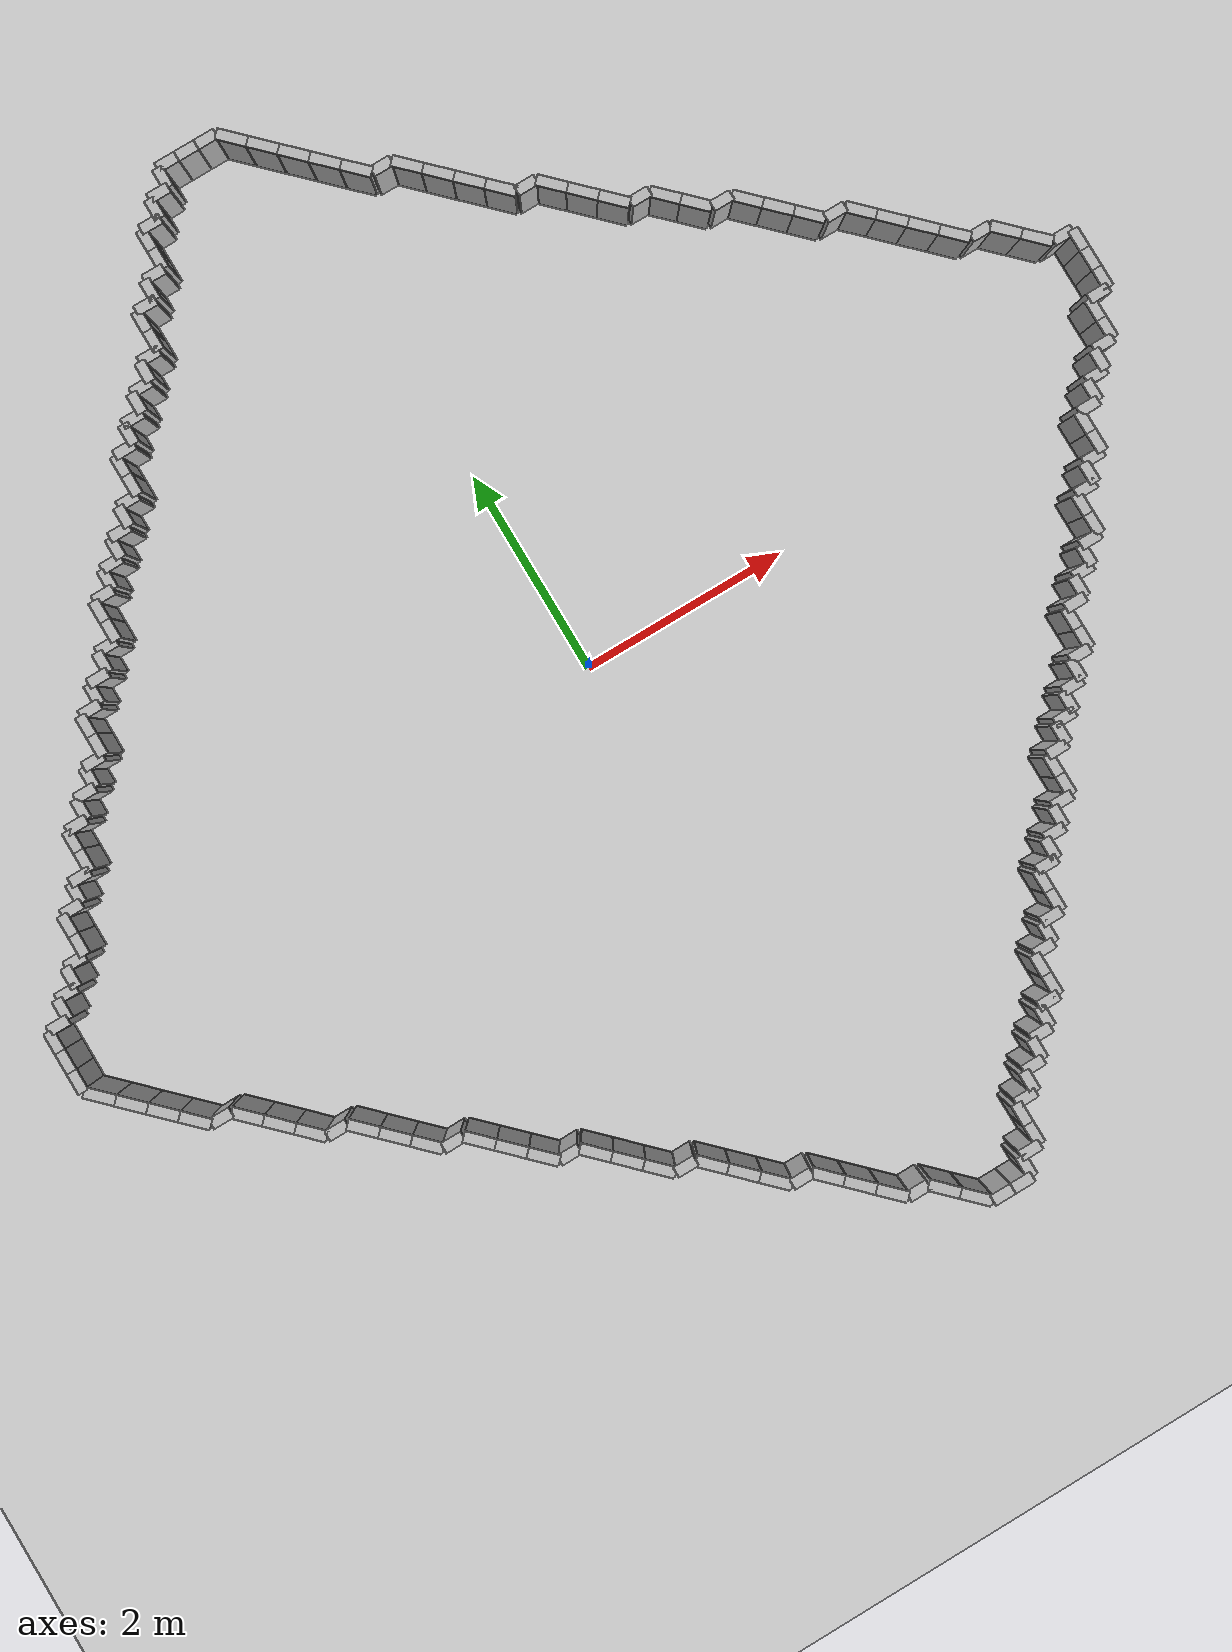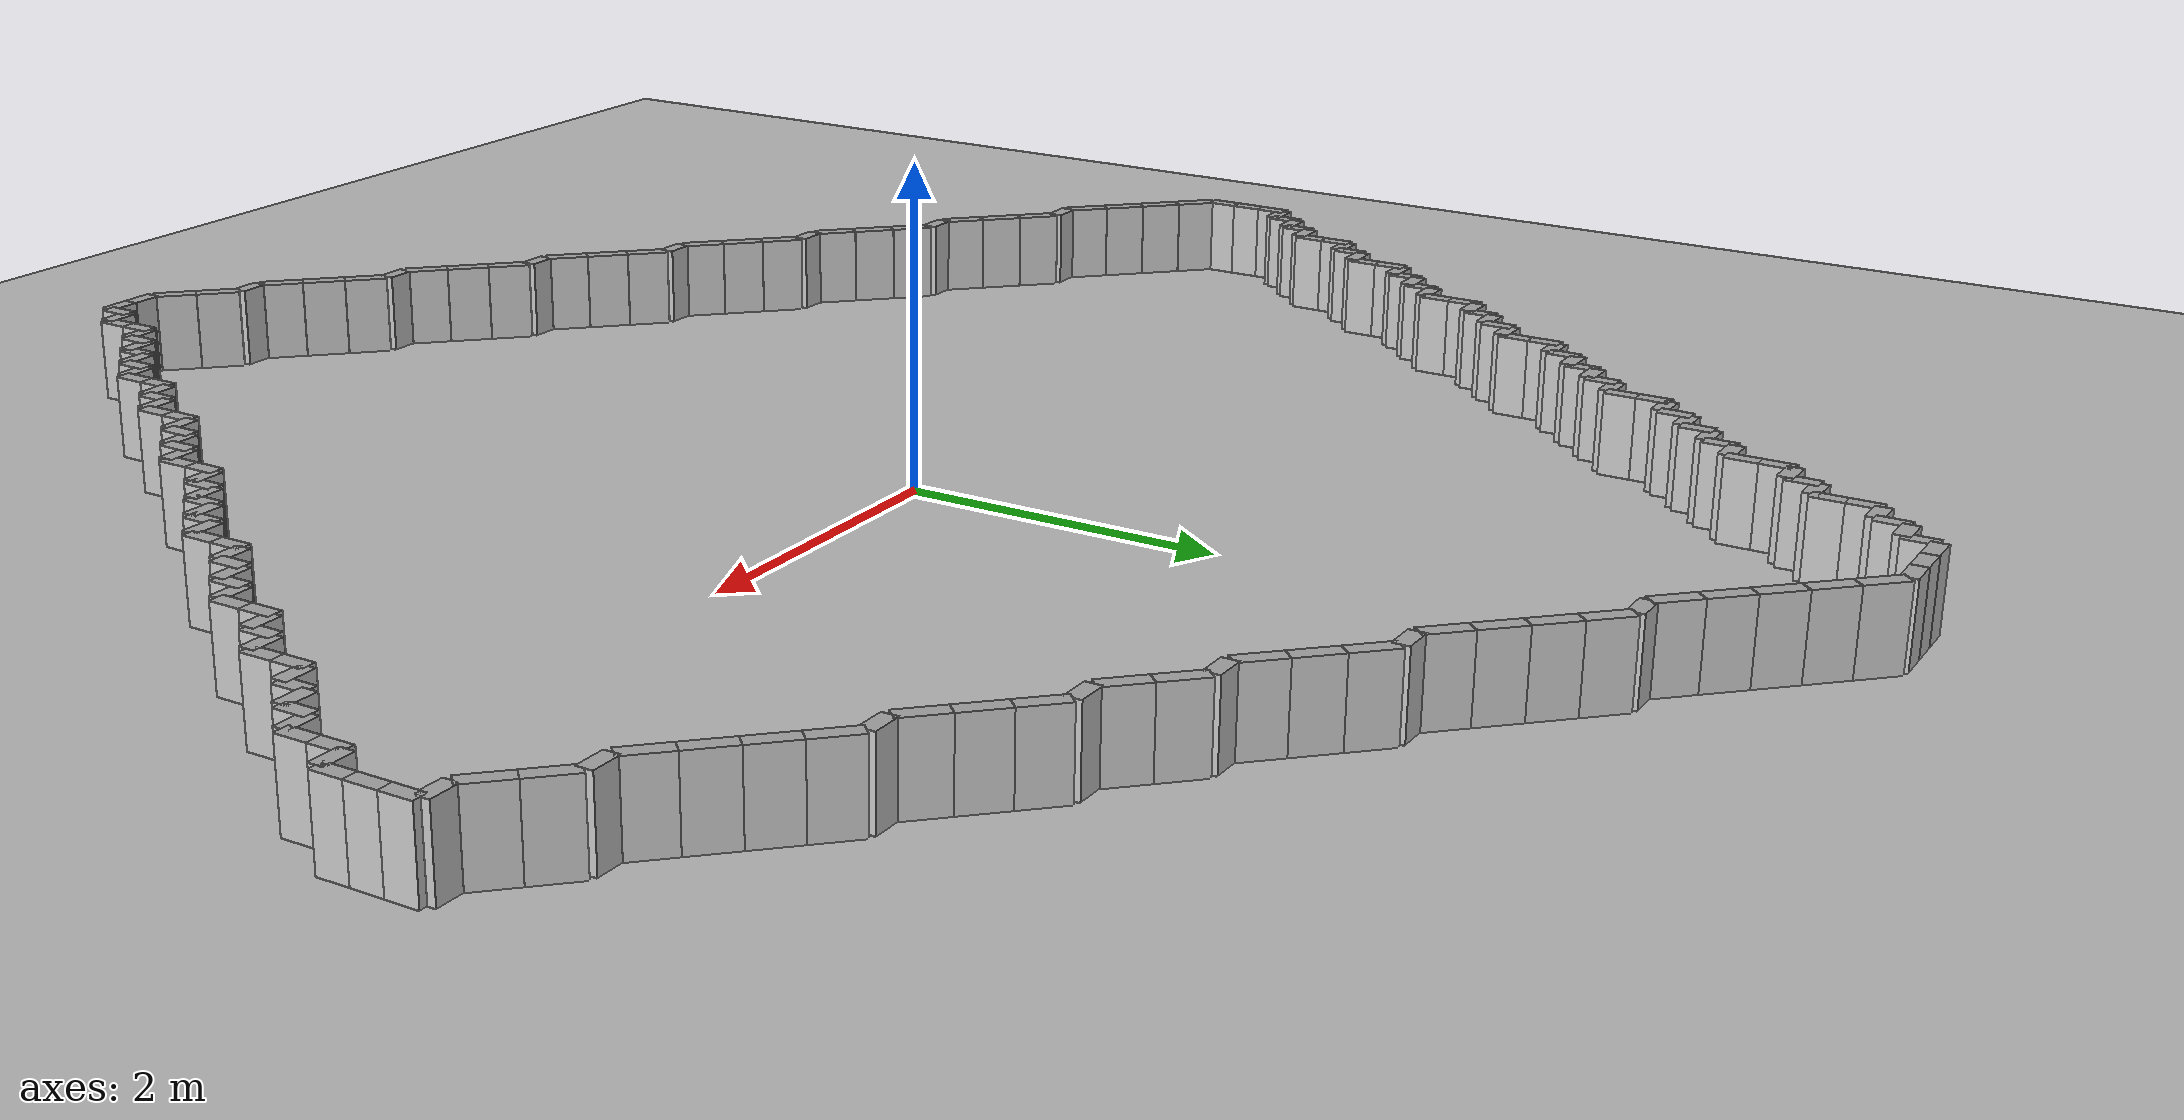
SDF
<?xml version="1.0" ?>
<!-- Gerado em: 2025-04-24 20:08:11 -->
<sdf version="1.6">
  <world name="default">
    <include>
      <uri>model://ground_plane</uri>
    </include>
    <include>
      <uri>model://sun</uri>
    </include>

    <model name="wall_0">
      <static>true</static>
      <pose>4.899803921568628 -0.30000000000000004 0 0 0 0.0019607818008702204</pose>
      <link name="link">
         <collision name="collision">
             <geometry>
                <box>
                  <size>0.20000038446714313 0.1 1</size>
                </box>
             </geometry>
         </collision>
         <visual name="visual">
             <geometry>
                <box>
                  <size>0.20000038446714313 0.1 1</size>
                </box>
             </geometry>
         </visual>
      </link>
    </model>

    <model name="wall_1">
      <static>true</static>
      <pose>4.999803921568628 -0.2 0 0 0 1.5707963267948966</pose>
      <link name="link">
         <collision name="collision">
             <geometry>
                <box>
                  <size>0.19960784313725524 0.1 1</size>
                </box>
             </geometry>
         </collision>
         <visual name="visual">
             <geometry>
                <box>
                  <size>0.19960784313725524 0.1 1</size>
                </box>
             </geometry>
         </visual>
      </link>
    </model>

    <model name="wall_2">
      <static>true</static>
      <pose>5.099803921568627 -0.1 0 0 0 0.001960781800869943</pose>
      <link name="link">
         <collision name="collision">
             <geometry>
                <box>
                  <size>0.20000038446714313 0.1 1</size>
                </box>
             </geometry>
         </collision>
         <visual name="visual">
             <geometry>
                <box>
                  <size>0.20000038446714313 0.1 1</size>
                </box>
             </geometry>
         </visual>
      </link>
    </model>

    <model name="wall_3">
      <static>true</static>
      <pose>5.199803921568628 0.0 0 0 0 1.5707963267948966</pose>
      <link name="link">
         <collision name="collision">
             <geometry>
                <box>
                  <size>0.19960784313725527 0.1 1</size>
                </box>
             </geometry>
         </collision>
         <visual name="visual">
             <geometry>
                <box>
                  <size>0.19960784313725527 0.1 1</size>
                </box>
             </geometry>
         </visual>
      </link>
    </model>

    <model name="wall_4">
      <static>true</static>
      <pose>5.299803921568628 0.1 0 0 0 0.001960781800869943</pose>
      <link name="link">
         <collision name="collision">
             <geometry>
                <box>
                  <size>0.20000038446714313 0.1 1</size>
                </box>
             </geometry>
         </collision>
         <visual name="visual">
             <geometry>
                <box>
                  <size>0.20000038446714313 0.1 1</size>
                </box>
             </geometry>
         </visual>
      </link>
    </model>

    <model name="wall_5">
      <static>true</static>
      <pose>5.399803921568628 0.2 0 0 0 1.5707963267948966</pose>
      <link name="link">
         <collision name="collision">
             <geometry>
                <box>
                  <size>0.19960784313725524 0.1 1</size>
                </box>
             </geometry>
         </collision>
         <visual name="visual">
             <geometry>
                <box>
                  <size>0.19960784313725524 0.1 1</size>
                </box>
             </geometry>
         </visual>
      </link>
    </model>

    <model name="wall_6">
      <static>true</static>
      <pose>5.399803921568628 0.39980392156862765 0 0 0 1.5707963267948966</pose>
      <link name="link">
         <collision name="collision">
             <geometry>
                <box>
                  <size>0.2 0.1 1</size>
                </box>
             </geometry>
         </collision>
         <visual name="visual">
             <geometry>
                <box>
                  <size>0.2 0.1 1</size>
                </box>
             </geometry>
         </visual>
      </link>
    </model>

    <model name="wall_7">
      <static>true</static>
      <pose>5.499803921568628 0.5 0 0 0 0.001960781800869943</pose>
      <link name="link">
         <collision name="collision">
             <geometry>
                <box>
                  <size>0.20000038446714313 0.1 1</size>
                </box>
             </geometry>
         </collision>
         <visual name="visual">
             <geometry>
                <box>
                  <size>0.20000038446714313 0.1 1</size>
                </box>
             </geometry>
         </visual>
      </link>
    </model>

    <model name="wall_8">
      <static>true</static>
      <pose>5.599803921568628 0.6000000000000001 0 0 0 1.5707963267948966</pose>
      <link name="link">
         <collision name="collision">
             <geometry>
                <box>
                  <size>0.19960784313725533 0.1 1</size>
                </box>
             </geometry>
         </collision>
         <visual name="visual">
             <geometry>
                <box>
                  <size>0.19960784313725533 0.1 1</size>
                </box>
             </geometry>
         </visual>
      </link>
    </model>

    <model name="wall_9">
      <static>true</static>
      <pose>5.599803921568628 0.7998039215686277 0 0 0 1.5707963267948966</pose>
      <link name="link">
         <collision name="collision">
             <geometry>
                <box>
                  <size>0.19999999999999996 0.1 1</size>
                </box>
             </geometry>
         </collision>
         <visual name="visual">
             <geometry>
                <box>
                  <size>0.19999999999999996 0.1 1</size>
                </box>
             </geometry>
         </visual>
      </link>
    </model>

    <model name="wall_10">
      <static>true</static>
      <pose>5.599803921568628 0.9998039215686276 0 0 0 1.5707963267948966</pose>
      <link name="link">
         <collision name="collision">
             <geometry>
                <box>
                  <size>0.20000000000000007 0.1 1</size>
                </box>
             </geometry>
         </collision>
         <visual name="visual">
             <geometry>
                <box>
                  <size>0.20000000000000007 0.1 1</size>
                </box>
             </geometry>
         </visual>
      </link>
    </model>

    <model name="wall_11">
      <static>true</static>
      <pose>5.499803921568628 1.0998039215686277 0 0 0 3.141592653589793</pose>
      <link name="link">
         <collision name="collision">
             <geometry>
                <box>
                  <size>0.20000000000000018 0.1 1</size>
                </box>
             </geometry>
         </collision>
         <visual name="visual">
             <geometry>
                <box>
                  <size>0.20000000000000018 0.1 1</size>
                </box>
             </geometry>
         </visual>
      </link>
    </model>

    <model name="wall_12">
      <static>true</static>
      <pose>5.299803921568628 1.1998039215686278 0 0 0 2.3561944901923453</pose>
      <link name="link">
         <collision name="collision">
             <geometry>
                <box>
                  <size>0.28284271247461906 0.1 1</size>
                </box>
             </geometry>
         </collision>
         <visual name="visual">
             <geometry>
                <box>
                  <size>0.28284271247461906 0.1 1</size>
                </box>
             </geometry>
         </visual>
      </link>
    </model>

    <model name="wall_13">
      <static>true</static>
      <pose>5.099803921568627 1.3998039215686275 0 0 0 2.3561944901923453</pose>
      <link name="link">
         <collision name="collision">
             <geometry>
                <box>
                  <size>0.28284271247461906 0.1 1</size>
                </box>
             </geometry>
         </collision>
         <visual name="visual">
             <geometry>
                <box>
                  <size>0.28284271247461906 0.1 1</size>
                </box>
             </geometry>
         </visual>
      </link>
    </model>

    <model name="wall_14">
      <static>true</static>
      <pose>4.899803921568628 1.4998039215686276 0 0 0 3.141592653589793</pose>
      <link name="link">
         <collision name="collision">
             <geometry>
                <box>
                  <size>0.20000000000000018 0.1 1</size>
                </box>
             </geometry>
         </collision>
         <visual name="visual">
             <geometry>
                <box>
                  <size>0.20000000000000018 0.1 1</size>
                </box>
             </geometry>
         </visual>
      </link>
    </model>

    <model name="wall_15">
      <static>true</static>
      <pose>4.699803921568628 1.5998039215686277 0 0 0 2.3561944901923426</pose>
      <link name="link">
         <collision name="collision">
             <geometry>
                <box>
                  <size>0.2828427124746186 0.1 1</size>
                </box>
             </geometry>
         </collision>
         <visual name="visual">
             <geometry>
                <box>
                  <size>0.2828427124746186 0.1 1</size>
                </box>
             </geometry>
         </visual>
      </link>
    </model>

    <model name="wall_16">
      <static>true</static>
      <pose>4.499803921568628 1.799803921568628 0 0 0 2.3561944901923453</pose>
      <link name="link">
         <collision name="collision">
             <geometry>
                <box>
                  <size>0.28284271247461906 0.1 1</size>
                </box>
             </geometry>
         </collision>
         <visual name="visual">
             <geometry>
                <box>
                  <size>0.28284271247461906 0.1 1</size>
                </box>
             </geometry>
         </visual>
      </link>
    </model>

    <model name="wall_17">
      <static>true</static>
      <pose>4.299803921568628 1.9998039215686276 0 0 0 2.3561944901923453</pose>
      <link name="link">
         <collision name="collision">
             <geometry>
                <box>
                  <size>0.28284271247461906 0.1 1</size>
                </box>
             </geometry>
         </collision>
         <visual name="visual">
             <geometry>
                <box>
                  <size>0.28284271247461906 0.1 1</size>
                </box>
             </geometry>
         </visual>
      </link>
    </model>

    <model name="wall_18">
      <static>true</static>
      <pose>4.099803921568627 2.199803921568628 0 0 0 2.356194490192345</pose>
      <link name="link">
         <collision name="collision">
             <geometry>
                <box>
                  <size>0.2828427124746193 0.1 1</size>
                </box>
             </geometry>
         </collision>
         <visual name="visual">
             <geometry>
                <box>
                  <size>0.2828427124746193 0.1 1</size>
                </box>
             </geometry>
         </visual>
      </link>
    </model>

    <model name="wall_19">
      <static>true</static>
      <pose>3.899803921568628 2.299803921568628 0 0 0 3.141592653589793</pose>
      <link name="link">
         <collision name="collision">
             <geometry>
                <box>
                  <size>0.19999999999999973 0.1 1</size>
                </box>
             </geometry>
         </collision>
         <visual name="visual">
             <geometry>
                <box>
                  <size>0.19999999999999973 0.1 1</size>
                </box>
             </geometry>
         </visual>
      </link>
    </model>

    <model name="wall_20">
      <static>true</static>
      <pose>3.699803921568628 2.399803921568628 0 0 0 2.356194490192346</pose>
      <link name="link">
         <collision name="collision">
             <geometry>
                <box>
                  <size>0.28284271247461895 0.1 1</size>
                </box>
             </geometry>
         </collision>
         <visual name="visual">
             <geometry>
                <box>
                  <size>0.28284271247461895 0.1 1</size>
                </box>
             </geometry>
         </visual>
      </link>
    </model>

    <model name="wall_21">
      <static>true</static>
      <pose>3.4998039215686276 2.5998039215686277 0 0 0 2.356194490192344</pose>
      <link name="link">
         <collision name="collision">
             <geometry>
                <box>
                  <size>0.28284271247461895 0.1 1</size>
                </box>
             </geometry>
         </collision>
         <visual name="visual">
             <geometry>
                <box>
                  <size>0.28284271247461895 0.1 1</size>
                </box>
             </geometry>
         </visual>
      </link>
    </model>

    <model name="wall_22">
      <static>true</static>
      <pose>3.299803921568628 2.799803921568628 0 0 0 2.356194490192345</pose>
      <link name="link">
         <collision name="collision">
             <geometry>
                <box>
                  <size>0.2828427124746193 0.1 1</size>
                </box>
             </geometry>
         </collision>
         <visual name="visual">
             <geometry>
                <box>
                  <size>0.2828427124746193 0.1 1</size>
                </box>
             </geometry>
         </visual>
      </link>
    </model>

    <model name="wall_23">
      <static>true</static>
      <pose>3.0998039215686277 2.899803921568628 0 0 0 3.141592653589793</pose>
      <link name="link">
         <collision name="collision">
             <geometry>
                <box>
                  <size>0.20000000000000018 0.1 1</size>
                </box>
             </geometry>
         </collision>
         <visual name="visual">
             <geometry>
                <box>
                  <size>0.20000000000000018 0.1 1</size>
                </box>
             </geometry>
         </visual>
      </link>
    </model>

    <model name="wall_24">
      <static>true</static>
      <pose>2.899803921568628 2.9998039215686276 0 0 0 2.356194490192345</pose>
      <link name="link">
         <collision name="collision">
             <geometry>
                <box>
                  <size>0.2828427124746186 0.1 1</size>
                </box>
             </geometry>
         </collision>
         <visual name="visual">
             <geometry>
                <box>
                  <size>0.2828427124746186 0.1 1</size>
                </box>
             </geometry>
         </visual>
      </link>
    </model>

    <model name="wall_25">
      <static>true</static>
      <pose>2.699803921568628 3.199803921568628 0 0 0 2.356194490192345</pose>
      <link name="link">
         <collision name="collision">
             <geometry>
                <box>
                  <size>0.2828427124746193 0.1 1</size>
                </box>
             </geometry>
         </collision>
         <visual name="visual">
             <geometry>
                <box>
                  <size>0.2828427124746193 0.1 1</size>
                </box>
             </geometry>
         </visual>
      </link>
    </model>

    <model name="wall_26">
      <static>true</static>
      <pose>2.4998039215686276 3.299803921568628 0 0 0 3.141592653589793</pose>
      <link name="link">
         <collision name="collision">
             <geometry>
                <box>
                  <size>0.20000000000000018 0.1 1</size>
                </box>
             </geometry>
         </collision>
         <visual name="visual">
             <geometry>
                <box>
                  <size>0.20000000000000018 0.1 1</size>
                </box>
             </geometry>
         </visual>
      </link>
    </model>

    <model name="wall_27">
      <static>true</static>
      <pose>2.2998039215686275 3.399803921568628 0 0 0 2.356194490192345</pose>
      <link name="link">
         <collision name="collision">
             <geometry>
                <box>
                  <size>0.2828427124746186 0.1 1</size>
                </box>
             </geometry>
         </collision>
         <visual name="visual">
             <geometry>
                <box>
                  <size>0.2828427124746186 0.1 1</size>
                </box>
             </geometry>
         </visual>
      </link>
    </model>

    <model name="wall_28">
      <static>true</static>
      <pose>2.0998039215686277 3.5998039215686277 0 0 0 2.356194490192345</pose>
      <link name="link">
         <collision name="collision">
             <geometry>
                <box>
                  <size>0.2828427124746193 0.1 1</size>
                </box>
             </geometry>
         </collision>
         <visual name="visual">
             <geometry>
                <box>
                  <size>0.2828427124746193 0.1 1</size>
                </box>
             </geometry>
         </visual>
      </link>
    </model>

    <model name="wall_29">
      <static>true</static>
      <pose>1.8998039215686275 3.799803921568628 0 0 0 2.3561944901923444</pose>
      <link name="link">
         <collision name="collision">
             <geometry>
                <box>
                  <size>0.28284271247461906 0.1 1</size>
                </box>
             </geometry>
         </collision>
         <visual name="visual">
             <geometry>
                <box>
                  <size>0.28284271247461906 0.1 1</size>
                </box>
             </geometry>
         </visual>
      </link>
    </model>

    <model name="wall_30">
      <static>true</static>
      <pose>1.6998039215686278 3.899803921568628 0 0 0 3.141592653589793</pose>
      <link name="link">
         <collision name="collision">
             <geometry>
                <box>
                  <size>0.19999999999999996 0.1 1</size>
                </box>
             </geometry>
         </collision>
         <visual name="visual">
             <geometry>
                <box>
                  <size>0.19999999999999996 0.1 1</size>
                </box>
             </geometry>
         </visual>
      </link>
    </model>

    <model name="wall_31">
      <static>true</static>
      <pose>1.4998039215686276 3.999803921568628 0 0 0 2.3561944901923444</pose>
      <link name="link">
         <collision name="collision">
             <geometry>
                <box>
                  <size>0.28284271247461906 0.1 1</size>
                </box>
             </geometry>
         </collision>
         <visual name="visual">
             <geometry>
                <box>
                  <size>0.28284271247461906 0.1 1</size>
                </box>
             </geometry>
         </visual>
      </link>
    </model>

    <model name="wall_32">
      <static>true</static>
      <pose>1.2998039215686277 4.199803921568628 0 0 0 2.356194490192347</pose>
      <link name="link">
         <collision name="collision">
             <geometry>
                <box>
                  <size>0.2828427124746186 0.1 1</size>
                </box>
             </geometry>
         </collision>
         <visual name="visual">
             <geometry>
                <box>
                  <size>0.2828427124746186 0.1 1</size>
                </box>
             </geometry>
         </visual>
      </link>
    </model>

    <model name="wall_33">
      <static>true</static>
      <pose>1.0998039215686277 4.399803921568628 0 0 0 2.3561944901923444</pose>
      <link name="link">
         <collision name="collision">
             <geometry>
                <box>
                  <size>0.28284271247461906 0.1 1</size>
                </box>
             </geometry>
         </collision>
         <visual name="visual">
             <geometry>
                <box>
                  <size>0.28284271247461906 0.1 1</size>
                </box>
             </geometry>
         </visual>
      </link>
    </model>

    <model name="wall_34">
      <static>true</static>
      <pose>0.8998039215686277 4.599803921568627 0 0 0 2.3561944901923444</pose>
      <link name="link">
         <collision name="collision">
             <geometry>
                <box>
                  <size>0.28284271247461906 0.1 1</size>
                </box>
             </geometry>
         </collision>
         <visual name="visual">
             <geometry>
                <box>
                  <size>0.28284271247461906 0.1 1</size>
                </box>
             </geometry>
         </visual>
      </link>
    </model>

    <model name="wall_35">
      <static>true</static>
      <pose>0.6998039215686276 4.699803921568628 0 0 0 3.141592653589793</pose>
      <link name="link">
         <collision name="collision">
             <geometry>
                <box>
                  <size>0.20000000000000007 0.1 1</size>
                </box>
             </geometry>
         </collision>
         <visual name="visual">
             <geometry>
                <box>
                  <size>0.20000000000000007 0.1 1</size>
                </box>
             </geometry>
         </visual>
      </link>
    </model>

    <model name="wall_36">
      <static>true</static>
      <pose>0.49980392156862763 4.799803921568628 0 0 0 2.3561944901923444</pose>
      <link name="link">
         <collision name="collision">
             <geometry>
                <box>
                  <size>0.28284271247461906 0.1 1</size>
                </box>
             </geometry>
         </collision>
         <visual name="visual">
             <geometry>
                <box>
                  <size>0.28284271247461906 0.1 1</size>
                </box>
             </geometry>
         </visual>
      </link>
    </model>

    <model name="wall_37">
      <static>true</static>
      <pose>0.2998039215686277 4.999803921568628 0 0 0 2.3561944901923444</pose>
      <link name="link">
         <collision name="collision">
             <geometry>
                <box>
                  <size>0.2828427124746191 0.1 1</size>
                </box>
             </geometry>
         </collision>
         <visual name="visual">
             <geometry>
                <box>
                  <size>0.2828427124746191 0.1 1</size>
                </box>
             </geometry>
         </visual>
      </link>
    </model>

    <model name="wall_38">
      <static>true</static>
      <pose>0.09980392156862763 5.199803921568629 0 0 0 2.3561944901923444</pose>
      <link name="link">
         <collision name="collision">
             <geometry>
                <box>
                  <size>0.2828427124746191 0.1 1</size>
                </box>
             </geometry>
         </collision>
         <visual name="visual">
             <geometry>
                <box>
                  <size>0.2828427124746191 0.1 1</size>
                </box>
             </geometry>
         </visual>
      </link>
    </model>

    <model name="wall_39">
      <static>true</static>
      <pose>-0.10019607843137238 5.399803921568628 0 0 0 2.3561944901923466</pose>
      <link name="link">
         <collision name="collision">
             <geometry>
                <box>
                  <size>0.2828427124746185 0.1 1</size>
                </box>
             </geometry>
         </collision>
         <visual name="visual">
             <geometry>
                <box>
                  <size>0.2828427124746185 0.1 1</size>
                </box>
             </geometry>
         </visual>
      </link>
    </model>

    <model name="wall_40">
      <static>true</static>
      <pose>-0.3001960784313724 5.599803921568627 0 0 0 2.3561944901923444</pose>
      <link name="link">
         <collision name="collision">
             <geometry>
                <box>
                  <size>0.2828427124746191 0.1 1</size>
                </box>
             </geometry>
         </collision>
         <visual name="visual">
             <geometry>
                <box>
                  <size>0.2828427124746191 0.1 1</size>
                </box>
             </geometry>
         </visual>
      </link>
    </model>

    <model name="wall_41">
      <static>true</static>
      <pose>-0.5001960784313724 5.699803921568628 0 0 0 3.141592653589793</pose>
      <link name="link">
         <collision name="collision">
             <geometry>
                <box>
                  <size>0.20000000000000007 0.1 1</size>
                </box>
             </geometry>
         </collision>
         <visual name="visual">
             <geometry>
                <box>
                  <size>0.20000000000000007 0.1 1</size>
                </box>
             </geometry>
         </visual>
      </link>
    </model>

    <model name="wall_42">
      <static>true</static>
      <pose>-0.7001960784313724 5.699803921568628 0 0 0 3.141592653589793</pose>
      <link name="link">
         <collision name="collision">
             <geometry>
                <box>
                  <size>0.19999999999999996 0.1 1</size>
                </box>
             </geometry>
         </collision>
         <visual name="visual">
             <geometry>
                <box>
                  <size>0.19999999999999996 0.1 1</size>
                </box>
             </geometry>
         </visual>
      </link>
    </model>

    <model name="wall_43">
      <static>true</static>
      <pose>-0.9 5.699803921568628 0 0 0 3.141592653589793</pose>
      <link name="link">
         <collision name="collision">
             <geometry>
                <box>
                  <size>0.19960784313725521 0.1 1</size>
                </box>
             </geometry>
         </collision>
         <visual name="visual">
             <geometry>
                <box>
                  <size>0.19960784313725521 0.1 1</size>
                </box>
             </geometry>
         </visual>
      </link>
    </model>

    <model name="wall_44">
      <static>true</static>
      <pose>-1.0 5.599803921568627 0 0 0 -1.5727571085957666</pose>
      <link name="link">
         <collision name="collision">
             <geometry>
                <box>
                  <size>0.20000038446714313 0.1 1</size>
                </box>
             </geometry>
         </collision>
         <visual name="visual">
             <geometry>
                <box>
                  <size>0.20000038446714313 0.1 1</size>
                </box>
             </geometry>
         </visual>
      </link>
    </model>

    <model name="wall_45">
      <static>true</static>
      <pose>-1.1 5.499803921568628 0 0 0 3.141592653589793</pose>
      <link name="link">
         <collision name="collision">
             <geometry>
                <box>
                  <size>0.19960784313725521 0.1 1</size>
                </box>
             </geometry>
         </collision>
         <visual name="visual">
             <geometry>
                <box>
                  <size>0.19960784313725521 0.1 1</size>
                </box>
             </geometry>
         </visual>
      </link>
    </model>

    <model name="wall_46">
      <static>true</static>
      <pose>-1.2000000000000002 5.399803921568628 0 0 0 -1.5727571085957677</pose>
      <link name="link">
         <collision name="collision">
             <geometry>
                <box>
                  <size>0.20000038446714224 0.1 1</size>
                </box>
             </geometry>
         </collision>
         <visual name="visual">
             <geometry>
                <box>
                  <size>0.20000038446714224 0.1 1</size>
                </box>
             </geometry>
         </visual>
      </link>
    </model>

    <model name="wall_47">
      <static>true</static>
      <pose>-1.3000000000000003 5.299803921568628 0 0 0 3.141592653589793</pose>
      <link name="link">
         <collision name="collision">
             <geometry>
                <box>
                  <size>0.19960784313725521 0.1 1</size>
                </box>
             </geometry>
         </collision>
         <visual name="visual">
             <geometry>
                <box>
                  <size>0.19960784313725521 0.1 1</size>
                </box>
             </geometry>
         </visual>
      </link>
    </model>

    <model name="wall_48">
      <static>true</static>
      <pose>-1.3998039215686278 5.199803921568629 0 0 0 -1.5707963267948966</pose>
      <link name="link">
         <collision name="collision">
             <geometry>
                <box>
                  <size>0.20000000000000018 0.1 1</size>
                </box>
             </geometry>
         </collision>
         <visual name="visual">
             <geometry>
                <box>
                  <size>0.20000000000000018 0.1 1</size>
                </box>
             </geometry>
         </visual>
      </link>
    </model>

    <model name="wall_49">
      <static>true</static>
      <pose>-1.4000000000000001 4.999803921568628 0 0 0 -1.5727571085957666</pose>
      <link name="link">
         <collision name="collision">
             <geometry>
                <box>
                  <size>0.20000038446714313 0.1 1</size>
                </box>
             </geometry>
         </collision>
         <visual name="visual">
             <geometry>
                <box>
                  <size>0.20000038446714313 0.1 1</size>
                </box>
             </geometry>
         </visual>
      </link>
    </model>

    <model name="wall_50">
      <static>true</static>
      <pose>-1.4999999999999998 4.899803921568628 0 0 0 3.141592653589793</pose>
      <link name="link">
         <collision name="collision">
             <geometry>
                <box>
                  <size>0.19960784313725455 0.1 1</size>
                </box>
             </geometry>
         </collision>
         <visual name="visual">
             <geometry>
                <box>
                  <size>0.19960784313725455 0.1 1</size>
                </box>
             </geometry>
         </visual>
      </link>
    </model>

    <model name="wall_51">
      <static>true</static>
      <pose>-1.5999999999999996 4.799803921568628 0 0 0 -1.57275710859577</pose>
      <link name="link">
         <collision name="collision">
             <geometry>
                <box>
                  <size>0.20000038446714313 0.1 1</size>
                </box>
             </geometry>
         </collision>
         <visual name="visual">
             <geometry>
                <box>
                  <size>0.20000038446714313 0.1 1</size>
                </box>
             </geometry>
         </visual>
      </link>
    </model>

    <model name="wall_52">
      <static>true</static>
      <pose>-1.6999999999999997 4.699803921568628 0 0 0 3.141592653589793</pose>
      <link name="link">
         <collision name="collision">
             <geometry>
                <box>
                  <size>0.19960784313725455 0.1 1</size>
                </box>
             </geometry>
         </collision>
         <visual name="visual">
             <geometry>
                <box>
                  <size>0.19960784313725455 0.1 1</size>
                </box>
             </geometry>
         </visual>
      </link>
    </model>

    <model name="wall_53">
      <static>true</static>
      <pose>-1.799803921568627 4.599803921568627 0 0 0 -1.5707963267948966</pose>
      <link name="link">
         <collision name="collision">
             <geometry>
                <box>
                  <size>0.20000000000000018 0.1 1</size>
                </box>
             </geometry>
         </collision>
         <visual name="visual">
             <geometry>
                <box>
                  <size>0.20000000000000018 0.1 1</size>
                </box>
             </geometry>
         </visual>
      </link>
    </model>

    <model name="wall_54">
      <static>true</static>
      <pose>-1.7999999999999998 4.399803921568628 0 0 0 -1.57275710859577</pose>
      <link name="link">
         <collision name="collision">
             <geometry>
                <box>
                  <size>0.20000038446714313 0.1 1</size>
                </box>
             </geometry>
         </collision>
         <visual name="visual">
             <geometry>
                <box>
                  <size>0.20000038446714313 0.1 1</size>
                </box>
             </geometry>
         </visual>
      </link>
    </model>

    <model name="wall_55">
      <static>true</static>
      <pose>-1.8999999999999997 4.2998039215686275 0 0 0 3.141592653589793</pose>
      <link name="link">
         <collision name="collision">
             <geometry>
                <box>
                  <size>0.19960784313725455 0.1 1</size>
                </box>
             </geometry>
         </collision>
         <visual name="visual">
             <geometry>
                <box>
                  <size>0.19960784313725455 0.1 1</size>
                </box>
             </geometry>
         </visual>
      </link>
    </model>

    <model name="wall_56">
      <static>true</static>
      <pose>-1.9999999999999996 4.199803921568628 0 0 0 -1.57275710859577</pose>
      <link name="link">
         <collision name="collision">
             <geometry>
                <box>
                  <size>0.20000038446714224 0.1 1</size>
                </box>
             </geometry>
         </collision>
         <visual name="visual">
             <geometry>
                <box>
                  <size>0.20000038446714224 0.1 1</size>
                </box>
             </geometry>
         </visual>
      </link>
    </model>

    <model name="wall_57">
      <static>true</static>
      <pose>-2.0999999999999996 4.099803921568628 0 0 0 3.141592653589793</pose>
      <link name="link">
         <collision name="collision">
             <geometry>
                <box>
                  <size>0.19960784313725455 0.1 1</size>
                </box>
             </geometry>
         </collision>
         <visual name="visual">
             <geometry>
                <box>
                  <size>0.19960784313725455 0.1 1</size>
                </box>
             </geometry>
         </visual>
      </link>
    </model>

    <model name="wall_58">
      <static>true</static>
      <pose>-2.1999999999999997 3.999803921568628 0 0 0 -1.572757108595771</pose>
      <link name="link">
         <collision name="collision">
             <geometry>
                <box>
                  <size>0.20000038446714313 0.1 1</size>
                </box>
             </geometry>
         </collision>
         <visual name="visual">
             <geometry>
                <box>
                  <size>0.20000038446714313 0.1 1</size>
                </box>
             </geometry>
         </visual>
      </link>
    </model>

    <model name="wall_59">
      <static>true</static>
      <pose>-2.3 3.899803921568628 0 0 0 3.141592653589793</pose>
      <link name="link">
         <collision name="collision">
             <geometry>
                <box>
                  <size>0.19960784313725455 0.1 1</size>
                </box>
             </geometry>
         </collision>
         <visual name="visual">
             <geometry>
                <box>
                  <size>0.19960784313725455 0.1 1</size>
                </box>
             </geometry>
         </visual>
      </link>
    </model>

    <model name="wall_60">
      <static>true</static>
      <pose>-2.4 3.799803921568628 0 0 0 -1.572757108595771</pose>
      <link name="link">
         <collision name="collision">
             <geometry>
                <box>
                  <size>0.20000038446714313 0.1 1</size>
                </box>
             </geometry>
         </collision>
         <visual name="visual">
             <geometry>
                <box>
                  <size>0.20000038446714313 0.1 1</size>
                </box>
             </geometry>
         </visual>
      </link>
    </model>

    <model name="wall_61">
      <static>true</static>
      <pose>-2.5 3.699803921568628 0 0 0 3.141592653589793</pose>
      <link name="link">
         <collision name="collision">
             <geometry>
                <box>
                  <size>0.19960784313725455 0.1 1</size>
                </box>
             </geometry>
         </collision>
         <visual name="visual">
             <geometry>
                <box>
                  <size>0.19960784313725455 0.1 1</size>
                </box>
             </geometry>
         </visual>
      </link>
    </model>

    <model name="wall_62">
      <static>true</static>
      <pose>-2.5998039215686273 3.5998039215686277 0 0 0 -1.5707963267948966</pose>
      <link name="link">
         <collision name="collision">
             <geometry>
                <box>
                  <size>0.20000000000000018 0.1 1</size>
                </box>
             </geometry>
         </collision>
         <visual name="visual">
             <geometry>
                <box>
                  <size>0.20000000000000018 0.1 1</size>
                </box>
             </geometry>
         </visual>
      </link>
    </model>

    <model name="wall_63">
      <static>true</static>
      <pose>-2.5999999999999996 3.399803921568628 0 0 0 -1.5727571085957688</pose>
      <link name="link">
         <collision name="collision">
             <geometry>
                <box>
                  <size>0.2000003844671427 0.1 1</size>
                </box>
             </geometry>
         </collision>
         <visual name="visual">
             <geometry>
                <box>
                  <size>0.2000003844671427 0.1 1</size>
                </box>
             </geometry>
         </visual>
      </link>
    </model>

    <model name="wall_64">
      <static>true</static>
      <pose>-2.6999999999999997 3.299803921568628 0 0 0 3.141592653589793</pose>
      <link name="link">
         <collision name="collision">
             <geometry>
                <box>
                  <size>0.19960784313725455 0.1 1</size>
                </box>
             </geometry>
         </collision>
         <visual name="visual">
             <geometry>
                <box>
                  <size>0.19960784313725455 0.1 1</size>
                </box>
             </geometry>
         </visual>
      </link>
    </model>

    <model name="wall_65">
      <static>true</static>
      <pose>-2.8 3.199803921568628 0 0 0 -1.572757108595771</pose>
      <link name="link">
         <collision name="collision">
             <geometry>
                <box>
                  <size>0.20000038446714313 0.1 1</size>
                </box>
             </geometry>
         </collision>
         <visual name="visual">
             <geometry>
                <box>
                  <size>0.20000038446714313 0.1 1</size>
                </box>
             </geometry>
         </visual>
      </link>
    </model>

    <model name="wall_66">
      <static>true</static>
      <pose>-2.9 3.0998039215686277 0 0 0 3.141592653589793</pose>
      <link name="link">
         <collision name="collision">
             <geometry>
                <box>
                  <size>0.19960784313725455 0.1 1</size>
                </box>
             </geometry>
         </collision>
         <visual name="visual">
             <geometry>
                <box>
                  <size>0.19960784313725455 0.1 1</size>
                </box>
             </geometry>
         </visual>
      </link>
    </model>

    <model name="wall_67">
      <static>true</static>
      <pose>-3.0 2.9998039215686276 0 0 0 -1.5727571085957688</pose>
      <link name="link">
         <collision name="collision">
             <geometry>
                <box>
                  <size>0.2000003844671427 0.1 1</size>
                </box>
             </geometry>
         </collision>
         <visual name="visual">
             <geometry>
                <box>
                  <size>0.2000003844671427 0.1 1</size>
                </box>
             </geometry>
         </visual>
      </link>
    </model>

    <model name="wall_68">
      <static>true</static>
      <pose>-3.0999999999999996 2.899803921568628 0 0 0 3.141592653589793</pose>
      <link name="link">
         <collision name="collision">
             <geometry>
                <box>
                  <size>0.19960784313725455 0.1 1</size>
                </box>
             </geometry>
         </collision>
         <visual name="visual">
             <geometry>
                <box>
                  <size>0.19960784313725455 0.1 1</size>
                </box>
             </geometry>
         </visual>
      </link>
    </model>

    <model name="wall_69">
      <static>true</static>
      <pose>-3.1999999999999997 2.799803921568628 0 0 0 -1.572757108595771</pose>
      <link name="link">
         <collision name="collision">
             <geometry>
                <box>
                  <size>0.20000038446714313 0.1 1</size>
                </box>
             </geometry>
         </collision>
         <visual name="visual">
             <geometry>
                <box>
                  <size>0.20000038446714313 0.1 1</size>
                </box>
             </geometry>
         </visual>
      </link>
    </model>

    <model name="wall_70">
      <static>true</static>
      <pose>-3.3 2.699803921568628 0 0 0 3.141592653589793</pose>
      <link name="link">
         <collision name="collision">
             <geometry>
                <box>
                  <size>0.19960784313725455 0.1 1</size>
                </box>
             </geometry>
         </collision>
         <visual name="visual">
             <geometry>
                <box>
                  <size>0.19960784313725455 0.1 1</size>
                </box>
             </geometry>
         </visual>
      </link>
    </model>

    <model name="wall_71">
      <static>true</static>
      <pose>-3.399803921568627 2.5998039215686277 0 0 0 -1.5707963267948966</pose>
      <link name="link">
         <collision name="collision">
             <geometry>
                <box>
                  <size>0.20000000000000018 0.1 1</size>
                </box>
             </geometry>
         </collision>
         <visual name="visual">
             <geometry>
                <box>
                  <size>0.20000000000000018 0.1 1</size>
                </box>
             </geometry>
         </visual>
      </link>
    </model>

    <model name="wall_72">
      <static>true</static>
      <pose>-3.4 2.399803921568628 0 0 0 -1.572757108595771</pose>
      <link name="link">
         <collision name="collision">
             <geometry>
                <box>
                  <size>0.2000003844671427 0.1 1</size>
                </box>
             </geometry>
         </collision>
         <visual name="visual">
             <geometry>
                <box>
                  <size>0.2000003844671427 0.1 1</size>
                </box>
             </geometry>
         </visual>
      </link>
    </model>

    <model name="wall_73">
      <static>true</static>
      <pose>-3.5 2.299803921568628 0 0 0 3.141592653589793</pose>
      <link name="link">
         <collision name="collision">
             <geometry>
                <box>
                  <size>0.19960784313725455 0.1 1</size>
                </box>
             </geometry>
         </collision>
         <visual name="visual">
             <geometry>
                <box>
                  <size>0.19960784313725455 0.1 1</size>
                </box>
             </geometry>
         </visual>
      </link>
    </model>

    <model name="wall_74">
      <static>true</static>
      <pose>-3.5999999999999996 2.199803921568628 0 0 0 -1.5727571085957688</pose>
      <link name="link">
         <collision name="collision">
             <geometry>
                <box>
                  <size>0.20000038446714313 0.1 1</size>
                </box>
             </geometry>
         </collision>
         <visual name="visual">
             <geometry>
                <box>
                  <size>0.20000038446714313 0.1 1</size>
                </box>
             </geometry>
         </visual>
      </link>
    </model>

    <model name="wall_75">
      <static>true</static>
      <pose>-3.6999999999999997 2.0998039215686277 0 0 0 3.141592653589793</pose>
      <link name="link">
         <collision name="collision">
             <geometry>
                <box>
                  <size>0.19960784313725455 0.1 1</size>
                </box>
             </geometry>
         </collision>
         <visual name="visual">
             <geometry>
                <box>
                  <size>0.19960784313725455 0.1 1</size>
                </box>
             </geometry>
         </visual>
      </link>
    </model>

    <model name="wall_76">
      <static>true</static>
      <pose>-3.8 1.9998039215686276 0 0 0 -1.572757108595771</pose>
      <link name="link">
         <collision name="collision">
             <geometry>
                <box>
                  <size>0.2000003844671429 0.1 1</size>
                </box>
             </geometry>
         </collision>
         <visual name="visual">
             <geometry>
                <box>
                  <size>0.2000003844671429 0.1 1</size>
                </box>
             </geometry>
         </visual>
      </link>
    </model>

    <model name="wall_77">
      <static>true</static>
      <pose>-3.9 1.8998039215686278 0 0 0 3.141592653589793</pose>
      <link name="link">
         <collision name="collision">
             <geometry>
                <box>
                  <size>0.19960784313725455 0.1 1</size>
                </box>
             </geometry>
         </collision>
         <visual name="visual">
             <geometry>
                <box>
                  <size>0.19960784313725455 0.1 1</size>
                </box>
             </geometry>
         </visual>
      </link>
    </model>

    <model name="wall_78">
      <static>true</static>
      <pose>-3.999803921568627 1.799803921568628 0 0 0 -1.5707963267948966</pose>
      <link name="link">
         <collision name="collision">
             <geometry>
                <box>
                  <size>0.19999999999999996 0.1 1</size>
                </box>
             </geometry>
         </collision>
         <visual name="visual">
             <geometry>
                <box>
                  <size>0.19999999999999996 0.1 1</size>
                </box>
             </geometry>
         </visual>
      </link>
    </model>

    <model name="wall_79">
      <static>true</static>
      <pose>-4.0 1.5998039215686277 0 0 0 -1.5727571085957688</pose>
      <link name="link">
         <collision name="collision">
             <geometry>
                <box>
                  <size>0.20000038446714313 0.1 1</size>
                </box>
             </geometry>
         </collision>
         <visual name="visual">
             <geometry>
                <box>
                  <size>0.20000038446714313 0.1 1</size>
                </box>
             </geometry>
         </visual>
      </link>
    </model>

    <model name="wall_80">
      <static>true</static>
      <pose>-4.1 1.4998039215686276 0 0 0 3.141592653589793</pose>
      <link name="link">
         <collision name="collision">
             <geometry>
                <box>
                  <size>0.19960784313725455 0.1 1</size>
                </box>
             </geometry>
         </collision>
         <visual name="visual">
             <geometry>
                <box>
                  <size>0.19960784313725455 0.1 1</size>
                </box>
             </geometry>
         </visual>
      </link>
    </model>

    <model name="wall_81">
      <static>true</static>
      <pose>-4.199999999999999 1.3998039215686275 0 0 0 -1.572757108595771</pose>
      <link name="link">
         <collision name="collision">
             <geometry>
                <box>
                  <size>0.2000003844671429 0.1 1</size>
                </box>
             </geometry>
         </collision>
         <visual name="visual">
             <geometry>
                <box>
                  <size>0.2000003844671429 0.1 1</size>
                </box>
             </geometry>
         </visual>
      </link>
    </model>

    <model name="wall_82">
      <static>true</static>
      <pose>-4.3 1.2998039215686277 0 0 0 3.141592653589793</pose>
      <link name="link">
         <collision name="collision">
             <geometry>
                <box>
                  <size>0.19960784313725455 0.1 1</size>
                </box>
             </geometry>
         </collision>
         <visual name="visual">
             <geometry>
                <box>
                  <size>0.19960784313725455 0.1 1</size>
                </box>
             </geometry>
         </visual>
      </link>
    </model>

    <model name="wall_83">
      <static>true</static>
      <pose>-4.4 1.1998039215686278 0 0 0 -1.572757108595771</pose>
      <link name="link">
         <collision name="collision">
             <geometry>
                <box>
                  <size>0.2000003844671429 0.1 1</size>
                </box>
             </geometry>
         </collision>
         <visual name="visual">
             <geometry>
                <box>
                  <size>0.2000003844671429 0.1 1</size>
                </box>
             </geometry>
         </visual>
      </link>
    </model>

    <model name="wall_84">
      <static>true</static>
      <pose>-4.5 1.0998039215686277 0 0 0 3.141592653589793</pose>
      <link name="link">
         <collision name="collision">
             <geometry>
                <box>
                  <size>0.19960784313725455 0.1 1</size>
                </box>
             </geometry>
         </collision>
         <visual name="visual">
             <geometry>
                <box>
                  <size>0.19960784313725455 0.1 1</size>
                </box>
             </geometry>
         </visual>
      </link>
    </model>

    <model name="wall_85">
      <static>true</static>
      <pose>-4.599803921568627 0.9998039215686276 0 0 0 -1.5707963267948966</pose>
      <link name="link">
         <collision name="collision">
             <geometry>
                <box>
                  <size>0.20000000000000007 0.1 1</size>
                </box>
             </geometry>
         </collision>
         <visual name="visual">
             <geometry>
                <box>
                  <size>0.20000000000000007 0.1 1</size>
                </box>
             </geometry>
         </visual>
      </link>
    </model>

    <model name="wall_86">
      <static>true</static>
      <pose>-4.6 0.7998039215686277 0 0 0 -1.572757108595771</pose>
      <link name="link">
         <collision name="collision">
             <geometry>
                <box>
                  <size>0.2000003844671429 0.1 1</size>
                </box>
             </geometry>
         </collision>
         <visual name="visual">
             <geometry>
                <box>
                  <size>0.2000003844671429 0.1 1</size>
                </box>
             </geometry>
         </visual>
      </link>
    </model>

    <model name="wall_87">
      <static>true</static>
      <pose>-4.7 0.6998039215686277 0 0 0 3.141592653589793</pose>
      <link name="link">
         <collision name="collision">
             <geometry>
                <box>
                  <size>0.19960784313725455 0.1 1</size>
                </box>
             </geometry>
         </collision>
         <visual name="visual">
             <geometry>
                <box>
                  <size>0.19960784313725455 0.1 1</size>
                </box>
             </geometry>
         </visual>
      </link>
    </model>

    <model name="wall_88">
      <static>true</static>
      <pose>-4.800000000000001 0.5998039215686277 0 0 0 -1.572757108595771</pose>
      <link name="link">
         <collision name="collision">
             <geometry>
                <box>
                  <size>0.20000038446714302 0.1 1</size>
                </box>
             </geometry>
         </collision>
         <visual name="visual">
             <geometry>
                <box>
                  <size>0.20000038446714302 0.1 1</size>
                </box>
             </geometry>
         </visual>
      </link>
    </model>

    <model name="wall_89">
      <static>true</static>
      <pose>-4.9 0.49980392156862763 0 0 0 3.141592653589793</pose>
      <link name="link">
         <collision name="collision">
             <geometry>
                <box>
                  <size>0.19960784313725455 0.1 1</size>
                </box>
             </geometry>
         </collision>
         <visual name="visual">
             <geometry>
                <box>
                  <size>0.19960784313725455 0.1 1</size>
                </box>
             </geometry>
         </visual>
      </link>
    </model>

    <model name="wall_90">
      <static>true</static>
      <pose>-4.999803921568628 0.39980392156862765 0 0 0 -1.5707963267948966</pose>
      <link name="link">
         <collision name="collision">
             <geometry>
                <box>
                  <size>0.2 0.1 1</size>
                </box>
             </geometry>
         </collision>
         <visual name="visual">
             <geometry>
                <box>
                  <size>0.2 0.1 1</size>
                </box>
             </geometry>
         </visual>
      </link>
    </model>

    <model name="wall_91">
      <static>true</static>
      <pose>-5.0 0.19980392156862764 0 0 0 -1.5727571085957666</pose>
      <link name="link">
         <collision name="collision">
             <geometry>
                <box>
                  <size>0.20000038446714294 0.1 1</size>
                </box>
             </geometry>
         </collision>
         <visual name="visual">
             <geometry>
                <box>
                  <size>0.20000038446714294 0.1 1</size>
                </box>
             </geometry>
         </visual>
      </link>
    </model>

    <model name="wall_92">
      <static>true</static>
      <pose>-5.1 0.09980392156862763 0 0 0 3.141592653589793</pose>
      <link name="link">
         <collision name="collision">
             <geometry>
                <box>
                  <size>0.19960784313725544 0.1 1</size>
                </box>
             </geometry>
         </collision>
         <visual name="visual">
             <geometry>
                <box>
                  <size>0.19960784313725544 0.1 1</size>
                </box>
             </geometry>
         </visual>
      </link>
    </model>

    <model name="wall_93">
      <static>true</static>
      <pose>-5.2 -0.0001960784313723707 0 0 0 -1.5727571085957666</pose>
      <link name="link">
         <collision name="collision">
             <geometry>
                <box>
                  <size>0.20000038446714297 0.1 1</size>
                </box>
             </geometry>
         </collision>
         <visual name="visual">
             <geometry>
                <box>
                  <size>0.20000038446714297 0.1 1</size>
                </box>
             </geometry>
         </visual>
      </link>
    </model>

    <model name="wall_94">
      <static>true</static>
      <pose>-5.300000000000001 -0.10019607843137238 0 0 0 3.141592653589793</pose>
      <link name="link">
         <collision name="collision">
             <geometry>
                <box>
                  <size>0.19960784313725544 0.1 1</size>
                </box>
             </geometry>
         </collision>
         <visual name="visual">
             <geometry>
                <box>
                  <size>0.19960784313725544 0.1 1</size>
                </box>
             </geometry>
         </visual>
      </link>
    </model>

    <model name="wall_95">
      <static>true</static>
      <pose>-5.4 -0.20019607843137238 0 0 0 -1.5727571085957666</pose>
      <link name="link">
         <collision name="collision">
             <geometry>
                <box>
                  <size>0.200000384467143 0.1 1</size>
                </box>
             </geometry>
         </collision>
         <visual name="visual">
             <geometry>
                <box>
                  <size>0.200000384467143 0.1 1</size>
                </box>
             </geometry>
         </visual>
      </link>
    </model>

    <model name="wall_96">
      <static>true</static>
      <pose>-5.5 -0.3001960784313724 0 0 0 3.141592653589793</pose>
      <link name="link">
         <collision name="collision">
             <geometry>
                <box>
                  <size>0.19960784313725544 0.1 1</size>
                </box>
             </geometry>
         </collision>
         <visual name="visual">
             <geometry>
                <box>
                  <size>0.19960784313725544 0.1 1</size>
                </box>
             </geometry>
         </visual>
      </link>
    </model>

    <model name="wall_97">
      <static>true</static>
      <pose>-5.599803921568628 -0.4001960784313724 0 0 0 -1.5707963267948966</pose>
      <link name="link">
         <collision name="collision">
             <geometry>
                <box>
                  <size>0.19999999999999996 0.1 1</size>
                </box>
             </geometry>
         </collision>
         <visual name="visual">
             <geometry>
                <box>
                  <size>0.19999999999999996 0.1 1</size>
                </box>
             </geometry>
         </visual>
      </link>
    </model>

    <model name="wall_98">
      <static>true</static>
      <pose>-5.599803921568628 -0.6001960784313725 0 0 0 -1.5707963267948966</pose>
      <link name="link">
         <collision name="collision">
             <geometry>
                <box>
                  <size>0.20000000000000007 0.1 1</size>
                </box>
             </geometry>
         </collision>
         <visual name="visual">
             <geometry>
                <box>
                  <size>0.20000000000000007 0.1 1</size>
                </box>
             </geometry>
         </visual>
      </link>
    </model>

    <model name="wall_99">
      <static>true</static>
      <pose>-5.599803921568628 -0.8001960784313724 0 0 0 -1.5707963267948966</pose>
      <link name="link">
         <collision name="collision">
             <geometry>
                <box>
                  <size>0.19999999999999996 0.1 1</size>
                </box>
             </geometry>
         </collision>
         <visual name="visual">
             <geometry>
                <box>
                  <size>0.19999999999999996 0.1 1</size>
                </box>
             </geometry>
         </visual>
      </link>
    </model>

    <model name="wall_100">
      <static>true</static>
      <pose>-5.5 -1.0 0 0 0 -0.7853981633974481</pose>
      <link name="link">
         <collision name="collision">
             <geometry>
                <box>
                  <size>0.2822881189207479 0.1 1</size>
                </box>
             </geometry>
         </collision>
         <visual name="visual">
             <geometry>
                <box>
                  <size>0.2822881189207479 0.1 1</size>
                </box>
             </geometry>
         </visual>
      </link>
    </model>

    <model name="wall_101">
      <static>true</static>
      <pose>-5.4 -1.1 0 0 0 -0.7853981633974483</pose>
      <link name="link">
         <collision name="collision">
             <geometry>
                <box>
                  <size>0.0005545935538712976 0.1 1</size>
                </box>
             </geometry>
         </collision>
         <visual name="visual">
             <geometry>
                <box>
                  <size>0.0005545935538712976 0.1 1</size>
                </box>
             </geometry>
         </visual>
      </link>
    </model>

    <model name="wall_102">
      <static>true</static>
      <pose>-5.300000000000001 -1.2000000000000002 0 0 0 -0.7853981633974477</pose>
      <link name="link">
         <collision name="collision">
             <geometry>
                <box>
                  <size>0.28228811892074784 0.1 1</size>
                </box>
             </geometry>
         </collision>
         <visual name="visual">
             <geometry>
                <box>
                  <size>0.28228811892074784 0.1 1</size>
                </box>
             </geometry>
         </visual>
      </link>
    </model>

    <model name="wall_103">
      <static>true</static>
      <pose>-5.2 -1.3 0 0 0 -0.7853981633974483</pose>
      <link name="link">
         <collision name="collision">
             <geometry>
                <box>
                  <size>0.0005545935538712976 0.1 1</size>
                </box>
             </geometry>
         </collision>
         <visual name="visual">
             <geometry>
                <box>
                  <size>0.0005545935538712976 0.1 1</size>
                </box>
             </geometry>
         </visual>
      </link>
    </model>

    <model name="wall_104">
      <static>true</static>
      <pose>-5.1 -1.3999999999999997 0 0 0 -0.7853981633974461</pose>
      <link name="link">
         <collision name="collision">
             <geometry>
                <box>
                  <size>0.28228811892074734 0.1 1</size>
                </box>
             </geometry>
         </collision>
         <visual name="visual">
             <geometry>
                <box>
                  <size>0.28228811892074734 0.1 1</size>
                </box>
             </geometry>
         </visual>
      </link>
    </model>

    <model name="wall_105">
      <static>true</static>
      <pose>-5.0 -1.4999999999999996 0 0 0 -0.7853981633982976</pose>
      <link name="link">
         <collision name="collision">
             <geometry>
                <box>
                  <size>0.0005545935538717686 0.1 1</size>
                </box>
             </geometry>
         </collision>
         <visual name="visual">
             <geometry>
                <box>
                  <size>0.0005545935538717686 0.1 1</size>
                </box>
             </geometry>
         </visual>
      </link>
    </model>

    <model name="wall_106">
      <static>true</static>
      <pose>-4.9 -1.5999999999999996 0 0 0 -0.7853981633974483</pose>
      <link name="link">
         <collision name="collision">
             <geometry>
                <box>
                  <size>0.2822881189207467 0.1 1</size>
                </box>
             </geometry>
         </collision>
         <visual name="visual">
             <geometry>
                <box>
                  <size>0.2822881189207467 0.1 1</size>
                </box>
             </geometry>
         </visual>
      </link>
    </model>

    <model name="wall_107">
      <static>true</static>
      <pose>-4.700196078431373 -1.699803921568627 0 0 0 0.0</pose>
      <link name="link">
         <collision name="collision">
             <geometry>
                <box>
                  <size>0.20000000000000018 0.1 1</size>
                </box>
             </geometry>
         </collision>
         <visual name="visual">
             <geometry>
                <box>
                  <size>0.20000000000000018 0.1 1</size>
                </box>
             </geometry>
         </visual>
      </link>
    </model>

    <model name="wall_108">
      <static>true</static>
      <pose>-4.6 -1.6999999999999997 0 0 0 -0.7853981633974483</pose>
      <link name="link">
         <collision name="collision">
             <geometry>
                <box>
                  <size>0.0005545935538725537 0.1 1</size>
                </box>
             </geometry>
         </collision>
         <visual name="visual">
             <geometry>
                <box>
                  <size>0.0005545935538725537 0.1 1</size>
                </box>
             </geometry>
         </visual>
      </link>
    </model>

    <model name="wall_109">
      <static>true</static>
      <pose>-4.5 -1.7999999999999998 0 0 0 -0.7853981633974483</pose>
      <link name="link">
         <collision name="collision">
             <geometry>
                <box>
                  <size>0.2822881189207467 0.1 1</size>
                </box>
             </geometry>
         </collision>
         <visual name="visual">
             <geometry>
                <box>
                  <size>0.2822881189207467 0.1 1</size>
                </box>
             </geometry>
         </visual>
      </link>
    </model>

    <model name="wall_110">
      <static>true</static>
      <pose>-4.4 -1.9 0 0 0 -0.7853981633971652</pose>
      <link name="link">
         <collision name="collision">
             <geometry>
                <box>
                  <size>0.0005545935538723967 0.1 1</size>
                </box>
             </geometry>
         </collision>
         <visual name="visual">
             <geometry>
                <box>
                  <size>0.0005545935538723967 0.1 1</size>
                </box>
             </geometry>
         </visual>
      </link>
    </model>

    <model name="wall_111">
      <static>true</static>
      <pose>-4.3 -1.9999999999999996 0 0 0 -0.7853981633974477</pose>
      <link name="link">
         <collision name="collision">
             <geometry>
                <box>
                  <size>0.28228811892074657 0.1 1</size>
                </box>
             </geometry>
         </collision>
         <visual name="visual">
             <geometry>
                <box>
                  <size>0.28228811892074657 0.1 1</size>
                </box>
             </geometry>
         </visual>
      </link>
    </model>

    <model name="wall_112">
      <static>true</static>
      <pose>-4.199999999999999 -2.0999999999999996 0 0 0 -0.7853981633974483</pose>
      <link name="link">
         <collision name="collision">
             <geometry>
                <box>
                  <size>0.0005545935538725537 0.1 1</size>
                </box>
             </geometry>
         </collision>
         <visual name="visual">
             <geometry>
                <box>
                  <size>0.0005545935538725537 0.1 1</size>
                </box>
             </geometry>
         </visual>
      </link>
    </model>

    <model name="wall_113">
      <static>true</static>
      <pose>-4.1 -2.1999999999999997 0 0 0 -0.7853981633974483</pose>
      <link name="link">
         <collision name="collision">
             <geometry>
                <box>
                  <size>0.2822881189207467 0.1 1</size>
                </box>
             </geometry>
         </collision>
         <visual name="visual">
             <geometry>
                <box>
                  <size>0.2822881189207467 0.1 1</size>
                </box>
             </geometry>
         </visual>
      </link>
    </model>

    <model name="wall_114">
      <static>true</static>
      <pose>-3.9001960784313727 -2.299803921568627 0 0 0 0.0</pose>
      <link name="link">
         <collision name="collision">
             <geometry>
                <box>
                  <size>0.19999999999999973 0.1 1</size>
                </box>
             </geometry>
         </collision>
         <visual name="visual">
             <geometry>
                <box>
                  <size>0.19999999999999973 0.1 1</size>
                </box>
             </geometry>
         </visual>
      </link>
    </model>

    <model name="wall_115">
      <static>true</static>
      <pose>-3.8 -2.3 0 0 0 -0.7853981633974483</pose>
      <link name="link">
         <collision name="collision">
             <geometry>
                <box>
                  <size>0.0005545935538725537 0.1 1</size>
                </box>
             </geometry>
         </collision>
         <visual name="visual">
             <geometry>
                <box>
                  <size>0.0005545935538725537 0.1 1</size>
                </box>
             </geometry>
         </visual>
      </link>
    </model>

    <model name="wall_116">
      <static>true</static>
      <pose>-3.6999999999999997 -2.4 0 0 0 -0.7853981633974483</pose>
      <link name="link">
         <collision name="collision">
             <geometry>
                <box>
                  <size>0.2822881189207467 0.1 1</size>
                </box>
             </geometry>
         </collision>
         <visual name="visual">
             <geometry>
                <box>
                  <size>0.2822881189207467 0.1 1</size>
                </box>
             </geometry>
         </visual>
      </link>
    </model>

    <model name="wall_117">
      <static>true</static>
      <pose>-3.5999999999999996 -2.5 0 0 0 -0.7853981633974483</pose>
      <link name="link">
         <collision name="collision">
             <geometry>
                <box>
                  <size>0.0005545935538719256 0.1 1</size>
                </box>
             </geometry>
         </collision>
         <visual name="visual">
             <geometry>
                <box>
                  <size>0.0005545935538719256 0.1 1</size>
                </box>
             </geometry>
         </visual>
      </link>
    </model>

    <model name="wall_118">
      <static>true</static>
      <pose>-3.5 -2.5999999999999996 0 0 0 -0.7853981633974483</pose>
      <link name="link">
         <collision name="collision">
             <geometry>
                <box>
                  <size>0.2822881189207467 0.1 1</size>
                </box>
             </geometry>
         </collision>
         <visual name="visual">
             <geometry>
                <box>
                  <size>0.2822881189207467 0.1 1</size>
                </box>
             </geometry>
         </visual>
      </link>
    </model>

    <model name="wall_119">
      <static>true</static>
      <pose>-3.4 -2.6999999999999997 0 0 0 -0.7853981633974483</pose>
      <link name="link">
         <collision name="collision">
             <geometry>
                <box>
                  <size>0.0005545935538725537 0.1 1</size>
                </box>
             </geometry>
         </collision>
         <visual name="visual">
             <geometry>
                <box>
                  <size>0.0005545935538725537 0.1 1</size>
                </box>
             </geometry>
         </visual>
      </link>
    </model>

    <model name="wall_120">
      <static>true</static>
      <pose>-3.3 -2.8 0 0 0 -0.7853981633974483</pose>
      <link name="link">
         <collision name="collision">
             <geometry>
                <box>
                  <size>0.2822881189207467 0.1 1</size>
                </box>
             </geometry>
         </collision>
         <visual name="visual">
             <geometry>
                <box>
                  <size>0.2822881189207467 0.1 1</size>
                </box>
             </geometry>
         </visual>
      </link>
    </model>

    <model name="wall_121">
      <static>true</static>
      <pose>-3.1001960784313725 -2.899803921568627 0 0 0 0.0</pose>
      <link name="link">
         <collision name="collision">
             <geometry>
                <box>
                  <size>0.20000000000000018 0.1 1</size>
                </box>
             </geometry>
         </collision>
         <visual name="visual">
             <geometry>
                <box>
                  <size>0.20000000000000018 0.1 1</size>
                </box>
             </geometry>
         </visual>
      </link>
    </model>

    <model name="wall_122">
      <static>true</static>
      <pose>-3.0 -2.9 0 0 0 -0.7853981633980145</pose>
      <link name="link">
         <collision name="collision">
             <geometry>
                <box>
                  <size>0.0005545935538722397 0.1 1</size>
                </box>
             </geometry>
         </collision>
         <visual name="visual">
             <geometry>
                <box>
                  <size>0.0005545935538722397 0.1 1</size>
                </box>
             </geometry>
         </visual>
      </link>
    </model>

    <model name="wall_123">
      <static>true</static>
      <pose>-2.9 -3.0 0 0 0 -0.7853981633974483</pose>
      <link name="link">
         <collision name="collision">
             <geometry>
                <box>
                  <size>0.2822881189207467 0.1 1</size>
                </box>
             </geometry>
         </collision>
         <visual name="visual">
             <geometry>
                <box>
                  <size>0.2822881189207467 0.1 1</size>
                </box>
             </geometry>
         </visual>
      </link>
    </model>

    <model name="wall_124">
      <static>true</static>
      <pose>-2.8 -3.0999999999999996 0 0 0 -0.7853981633968821</pose>
      <link name="link">
         <collision name="collision">
             <geometry>
                <box>
                  <size>0.0005545935538722397 0.1 1</size>
                </box>
             </geometry>
         </collision>
         <visual name="visual">
             <geometry>
                <box>
                  <size>0.0005545935538722397 0.1 1</size>
                </box>
             </geometry>
         </visual>
      </link>
    </model>

    <model name="wall_125">
      <static>true</static>
      <pose>-2.6999999999999997 -3.1999999999999997 0 0 0 -0.7853981633974483</pose>
      <link name="link">
         <collision name="collision">
             <geometry>
                <box>
                  <size>0.2822881189207467 0.1 1</size>
                </box>
             </geometry>
         </collision>
         <visual name="visual">
             <geometry>
                <box>
                  <size>0.2822881189207467 0.1 1</size>
                </box>
             </geometry>
         </visual>
      </link>
    </model>

    <model name="wall_126">
      <static>true</static>
      <pose>-2.5999999999999996 -3.3 0 0 0 -0.7853981633980145</pose>
      <link name="link">
         <collision name="collision">
             <geometry>
                <box>
                  <size>0.0005545935538722397 0.1 1</size>
                </box>
             </geometry>
         </collision>
         <visual name="visual">
             <geometry>
                <box>
                  <size>0.0005545935538722397 0.1 1</size>
                </box>
             </geometry>
         </visual>
      </link>
    </model>

    <model name="wall_127">
      <static>true</static>
      <pose>-2.5 -3.4 0 0 0 -0.7853981633974483</pose>
      <link name="link">
         <collision name="collision">
             <geometry>
                <box>
                  <size>0.2822881189207467 0.1 1</size>
                </box>
             </geometry>
         </collision>
         <visual name="visual">
             <geometry>
                <box>
                  <size>0.2822881189207467 0.1 1</size>
                </box>
             </geometry>
         </visual>
      </link>
    </model>

    <model name="wall_128">
      <static>true</static>
      <pose>-2.3001960784313726 -3.499803921568627 0 0 0 0.0</pose>
      <link name="link">
         <collision name="collision">
             <geometry>
                <box>
                  <size>0.20000000000000018 0.1 1</size>
                </box>
             </geometry>
         </collision>
         <visual name="visual">
             <geometry>
                <box>
                  <size>0.20000000000000018 0.1 1</size>
                </box>
             </geometry>
         </visual>
      </link>
    </model>

    <model name="wall_129">
      <static>true</static>
      <pose>-2.1999999999999997 -3.5 0 0 0 -0.7853981633968821</pose>
      <link name="link">
         <collision name="collision">
             <geometry>
                <box>
                  <size>0.0005545935538722397 0.1 1</size>
                </box>
             </geometry>
         </collision>
         <visual name="visual">
             <geometry>
                <box>
                  <size>0.0005545935538722397 0.1 1</size>
                </box>
             </geometry>
         </visual>
      </link>
    </model>

    <model name="wall_130">
      <static>true</static>
      <pose>-2.0999999999999996 -3.5999999999999996 0 0 0 -0.7853981633974483</pose>
      <link name="link">
         <collision name="collision">
             <geometry>
                <box>
                  <size>0.2822881189207467 0.1 1</size>
                </box>
             </geometry>
         </collision>
         <visual name="visual">
             <geometry>
                <box>
                  <size>0.2822881189207467 0.1 1</size>
                </box>
             </geometry>
         </visual>
      </link>
    </model>

    <model name="wall_131">
      <static>true</static>
      <pose>-1.9999999999999996 -3.6999999999999997 0 0 0 -0.7853981633977314</pose>
      <link name="link">
         <collision name="collision">
             <geometry>
                <box>
                  <size>0.0005545935538723967 0.1 1</size>
                </box>
             </geometry>
         </collision>
         <visual name="visual">
             <geometry>
                <box>
                  <size>0.0005545935538723967 0.1 1</size>
                </box>
             </geometry>
         </visual>
      </link>
    </model>

    <model name="wall_132">
      <static>true</static>
      <pose>-1.8999999999999997 -3.8 0 0 0 -0.7853981633974483</pose>
      <link name="link">
         <collision name="collision">
             <geometry>
                <box>
                  <size>0.2822881189207467 0.1 1</size>
                </box>
             </geometry>
         </collision>
         <visual name="visual">
             <geometry>
                <box>
                  <size>0.2822881189207467 0.1 1</size>
                </box>
             </geometry>
         </visual>
      </link>
    </model>

    <model name="wall_133">
      <static>true</static>
      <pose>-1.7999999999999998 -3.9 0 0 0 -0.7853981633977314</pose>
      <link name="link">
         <collision name="collision">
             <geometry>
                <box>
                  <size>0.0005545935538723967 0.1 1</size>
                </box>
             </geometry>
         </collision>
         <visual name="visual">
             <geometry>
                <box>
                  <size>0.0005545935538723967 0.1 1</size>
                </box>
             </geometry>
         </visual>
      </link>
    </model>

    <model name="wall_134">
      <static>true</static>
      <pose>-1.6999999999999997 -4.0 0 0 0 -0.7853981633974483</pose>
      <link name="link">
         <collision name="collision">
             <geometry>
                <box>
                  <size>0.2822881189207467 0.1 1</size>
                </box>
             </geometry>
         </collision>
         <visual name="visual">
             <geometry>
                <box>
                  <size>0.2822881189207467 0.1 1</size>
                </box>
             </geometry>
         </visual>
      </link>
    </model>

    <model name="wall_135">
      <static>true</static>
      <pose>-1.5001960784313724 -4.099803921568627 0 0 0 0.0</pose>
      <link name="link">
         <collision name="collision">
             <geometry>
                <box>
                  <size>0.19999999999999996 0.1 1</size>
                </box>
             </geometry>
         </collision>
         <visual name="visual">
             <geometry>
                <box>
                  <size>0.19999999999999996 0.1 1</size>
                </box>
             </geometry>
         </visual>
      </link>
    </model>

    <model name="wall_136">
      <static>true</static>
      <pose>-1.4000000000000001 -4.1 0 0 0 -0.7853981633985807</pose>
      <link name="link">
         <collision name="collision">
             <geometry>
                <box>
                  <size>0.0005545935538719256 0.1 1</size>
                </box>
             </geometry>
         </collision>
         <visual name="visual">
             <geometry>
                <box>
                  <size>0.0005545935538719256 0.1 1</size>
                </box>
             </geometry>
         </visual>
      </link>
    </model>

    <model name="wall_137">
      <static>true</static>
      <pose>-1.3000000000000003 -4.2 0 0 0 -0.7853981633974466</pose>
      <link name="link">
         <collision name="collision">
             <geometry>
                <box>
                  <size>0.2822881189207472 0.1 1</size>
                </box>
             </geometry>
         </collision>
         <visual name="visual">
             <geometry>
                <box>
                  <size>0.2822881189207472 0.1 1</size>
                </box>
             </geometry>
         </visual>
      </link>
    </model>

    <model name="wall_138">
      <static>true</static>
      <pose>-1.2000000000000002 -4.3 0 0 0 -0.7853981633971652</pose>
      <link name="link">
         <collision name="collision">
             <geometry>
                <box>
                  <size>0.0005545935538714546 0.1 1</size>
                </box>
             </geometry>
         </collision>
         <visual name="visual">
             <geometry>
                <box>
                  <size>0.0005545935538714546 0.1 1</size>
                </box>
             </geometry>
         </visual>
      </link>
    </model>

    <model name="wall_139">
      <static>true</static>
      <pose>-1.1 -4.3999999999999995 0 0 0 -0.7853981633974466</pose>
      <link name="link">
         <collision name="collision">
             <geometry>
                <box>
                  <size>0.2822881189207472 0.1 1</size>
                </box>
             </geometry>
         </collision>
         <visual name="visual">
             <geometry>
                <box>
                  <size>0.2822881189207472 0.1 1</size>
                </box>
             </geometry>
         </visual>
      </link>
    </model>

    <model name="wall_140">
      <static>true</static>
      <pose>-1.0 -4.5 0 0 0 -0.7853981633985807</pose>
      <link name="link">
         <collision name="collision">
             <geometry>
                <box>
                  <size>0.0005545935538719256 0.1 1</size>
                </box>
             </geometry>
         </collision>
         <visual name="visual">
             <geometry>
                <box>
                  <size>0.0005545935538719256 0.1 1</size>
                </box>
             </geometry>
         </visual>
      </link>
    </model>

    <model name="wall_141">
      <static>true</static>
      <pose>-0.9 -4.6 0 0 0 -0.7853981633974488</pose>
      <link name="link">
         <collision name="collision">
             <geometry>
                <box>
                  <size>0.28228811892074784 0.1 1</size>
                </box>
             </geometry>
         </collision>
         <visual name="visual">
             <geometry>
                <box>
                  <size>0.28228811892074784 0.1 1</size>
                </box>
             </geometry>
         </visual>
      </link>
    </model>

    <model name="wall_142">
      <static>true</static>
      <pose>-0.7001960784313724 -4.699803921568628 0 0 0 0.0</pose>
      <link name="link">
         <collision name="collision">
             <geometry>
                <box>
                  <size>0.19999999999999996 0.1 1</size>
                </box>
             </geometry>
         </collision>
         <visual name="visual">
             <geometry>
                <box>
                  <size>0.19999999999999996 0.1 1</size>
                </box>
             </geometry>
         </visual>
      </link>
    </model>

    <model name="wall_143">
      <static>true</static>
      <pose>-0.6000000000000001 -4.7 0 0 0 -0.7853981633973067</pose>
      <link name="link">
         <collision name="collision">
             <geometry>
                <box>
                  <size>0.0005545935538713761 0.1 1</size>
                </box>
             </geometry>
         </collision>
         <visual name="visual">
             <geometry>
                <box>
                  <size>0.0005545935538713761 0.1 1</size>
                </box>
             </geometry>
         </visual>
      </link>
    </model>

    <model name="wall_144">
      <static>true</static>
      <pose>-0.5 -4.800000000000001 0 0 0 -0.7853981633974488</pose>
      <link name="link">
         <collision name="collision">
             <geometry>
                <box>
                  <size>0.28228811892074784 0.1 1</size>
                </box>
             </geometry>
         </collision>
         <visual name="visual">
             <geometry>
                <box>
                  <size>0.28228811892074784 0.1 1</size>
                </box>
             </geometry>
         </visual>
      </link>
    </model>

    <model name="wall_145">
      <static>true</static>
      <pose>-0.4 -4.9 0 0 0 -0.7853981633974483</pose>
      <link name="link">
         <collision name="collision">
             <geometry>
                <box>
                  <size>0.0005545935538712976 0.1 1</size>
                </box>
             </geometry>
         </collision>
         <visual name="visual">
             <geometry>
                <box>
                  <size>0.0005545935538712976 0.1 1</size>
                </box>
             </geometry>
         </visual>
      </link>
    </model>

    <model name="wall_146">
      <static>true</static>
      <pose>-0.30000000000000004 -5.0 0 0 0 -0.7853981633974487</pose>
      <link name="link">
         <collision name="collision">
             <geometry>
                <box>
                  <size>0.28228811892074784 0.1 1</size>
                </box>
             </geometry>
         </collision>
         <visual name="visual">
             <geometry>
                <box>
                  <size>0.28228811892074784 0.1 1</size>
                </box>
             </geometry>
         </visual>
      </link>
    </model>

    <model name="wall_147">
      <static>true</static>
      <pose>-0.2 -5.1000000000000005 0 0 0 -0.7853981633974483</pose>
      <link name="link">
         <collision name="collision">
             <geometry>
                <box>
                  <size>0.0005545935538712976 0.1 1</size>
                </box>
             </geometry>
         </collision>
         <visual name="visual">
             <geometry>
                <box>
                  <size>0.0005545935538712976 0.1 1</size>
                </box>
             </geometry>
         </visual>
      </link>
    </model>

    <model name="wall_148">
      <static>true</static>
      <pose>-0.1 -5.200000000000001 0 0 0 -0.7853981633974487</pose>
      <link name="link">
         <collision name="collision">
             <geometry>
                <box>
                  <size>0.28228811892074784 0.1 1</size>
                </box>
             </geometry>
         </collision>
         <visual name="visual">
             <geometry>
                <box>
                  <size>0.28228811892074784 0.1 1</size>
                </box>
             </geometry>
         </visual>
      </link>
    </model>

    <model name="wall_149">
      <static>true</static>
      <pose>0.09980392156862763 -5.299803921568628 0 0 0 0.0</pose>
      <link name="link">
         <collision name="collision">
             <geometry>
                <box>
                  <size>0.2 0.1 1</size>
                </box>
             </geometry>
         </collision>
         <visual name="visual">
             <geometry>
                <box>
                  <size>0.2 0.1 1</size>
                </box>
             </geometry>
         </visual>
      </link>
    </model>

    <model name="wall_150">
      <static>true</static>
      <pose>0.2 -5.300000000000001 0 0 0 -0.7853981633974483</pose>
      <link name="link">
         <collision name="collision">
             <geometry>
                <box>
                  <size>0.0005545935538712976 0.1 1</size>
                </box>
             </geometry>
         </collision>
         <visual name="visual">
             <geometry>
                <box>
                  <size>0.0005545935538712976 0.1 1</size>
                </box>
             </geometry>
         </visual>
      </link>
    </model>

    <model name="wall_151">
      <static>true</static>
      <pose>0.30000000000000004 -5.4 0 0 0 -0.7853981633974465</pose>
      <link name="link">
         <collision name="collision">
             <geometry>
                <box>
                  <size>0.28228811892074723 0.1 1</size>
                </box>
             </geometry>
         </collision>
         <visual name="visual">
             <geometry>
                <box>
                  <size>0.28228811892074723 0.1 1</size>
                </box>
             </geometry>
         </visual>
      </link>
    </model>

    <model name="wall_152">
      <static>true</static>
      <pose>0.4 -5.5 0 0 0 -0.7853981633974483</pose>
      <link name="link">
         <collision name="collision">
             <geometry>
                <box>
                  <size>0.0005545935538712976 0.1 1</size>
                </box>
             </geometry>
         </collision>
         <visual name="visual">
             <geometry>
                <box>
                  <size>0.0005545935538712976 0.1 1</size>
                </box>
             </geometry>
         </visual>
      </link>
    </model>

    <model name="wall_153">
      <static>true</static>
      <pose>0.5 -5.6 0 0 0 -0.7853981633974488</pose>
      <link name="link">
         <collision name="collision">
             <geometry>
                <box>
                  <size>0.28228811892074784 0.1 1</size>
                </box>
             </geometry>
         </collision>
         <visual name="visual">
             <geometry>
                <box>
                  <size>0.28228811892074784 0.1 1</size>
                </box>
             </geometry>
         </visual>
      </link>
    </model>

    <model name="wall_154">
      <static>true</static>
      <pose>0.6998039215686276 -5.699803921568628 0 0 0 0.0</pose>
      <link name="link">
         <collision name="collision">
             <geometry>
                <box>
                  <size>0.20000000000000007 0.1 1</size>
                </box>
             </geometry>
         </collision>
         <visual name="visual">
             <geometry>
                <box>
                  <size>0.20000000000000007 0.1 1</size>
                </box>
             </geometry>
         </visual>
      </link>
    </model>

    <model name="wall_155">
      <static>true</static>
      <pose>0.8998039215686277 -5.699803921568628 0 0 0 0.0</pose>
      <link name="link">
         <collision name="collision">
             <geometry>
                <box>
                  <size>0.19999999999999996 0.1 1</size>
                </box>
             </geometry>
         </collision>
         <visual name="visual">
             <geometry>
                <box>
                  <size>0.19999999999999996 0.1 1</size>
                </box>
             </geometry>
         </visual>
      </link>
    </model>

    <model name="wall_156">
      <static>true</static>
      <pose>0.9998039215686276 -5.6 0 0 0 1.5707963267948966</pose>
      <link name="link">
         <collision name="collision">
             <geometry>
                <box>
                  <size>0.19960784313725544 0.1 1</size>
                </box>
             </geometry>
         </collision>
         <visual name="visual">
             <geometry>
                <box>
                  <size>0.19960784313725544 0.1 1</size>
                </box>
             </geometry>
         </visual>
      </link>
    </model>

    <model name="wall_157">
      <static>true</static>
      <pose>1.0998039215686277 -5.5 0 0 0 0.001960781800869945</pose>
      <link name="link">
         <collision name="collision">
             <geometry>
                <box>
                  <size>0.2000003844671429 0.1 1</size>
                </box>
             </geometry>
         </collision>
         <visual name="visual">
             <geometry>
                <box>
                  <size>0.2000003844671429 0.1 1</size>
                </box>
             </geometry>
         </visual>
      </link>
    </model>

    <model name="wall_158">
      <static>true</static>
      <pose>1.1998039215686276 -5.4 0 0 0 1.5707963267948966</pose>
      <link name="link">
         <collision name="collision">
             <geometry>
                <box>
                  <size>0.19960784313725455 0.1 1</size>
                </box>
             </geometry>
         </collision>
         <visual name="visual">
             <geometry>
                <box>
                  <size>0.19960784313725455 0.1 1</size>
                </box>
             </geometry>
         </visual>
      </link>
    </model>

    <model name="wall_159">
      <static>true</static>
      <pose>1.1998039215686276 -5.200196078431373 0 0 0 1.5707963267948966</pose>
      <link name="link">
         <collision name="collision">
             <geometry>
                <box>
                  <size>0.20000000000000018 0.1 1</size>
                </box>
             </geometry>
         </collision>
         <visual name="visual">
             <geometry>
                <box>
                  <size>0.20000000000000018 0.1 1</size>
                </box>
             </geometry>
         </visual>
      </link>
    </model>

    <model name="wall_160">
      <static>true</static>
      <pose>1.2998039215686277 -5.1000000000000005 0 0 0 0.001960781800869943</pose>
      <link name="link">
         <collision name="collision">
             <geometry>
                <box>
                  <size>0.20000038446714313 0.1 1</size>
                </box>
             </geometry>
         </collision>
         <visual name="visual">
             <geometry>
                <box>
                  <size>0.20000038446714313 0.1 1</size>
                </box>
             </geometry>
         </visual>
      </link>
    </model>

    <model name="wall_161">
      <static>true</static>
      <pose>1.3998039215686278 -5.0 0 0 0 1.5707963267948966</pose>
      <link name="link">
         <collision name="collision">
             <geometry>
                <box>
                  <size>0.19960784313725544 0.1 1</size>
                </box>
             </geometry>
         </collision>
         <visual name="visual">
             <geometry>
                <box>
                  <size>0.19960784313725544 0.1 1</size>
                </box>
             </geometry>
         </visual>
      </link>
    </model>

    <model name="wall_162">
      <static>true</static>
      <pose>1.4998039215686276 -4.9 0 0 0 0.001960781800869945</pose>
      <link name="link">
         <collision name="collision">
             <geometry>
                <box>
                  <size>0.2000003844671429 0.1 1</size>
                </box>
             </geometry>
         </collision>
         <visual name="visual">
             <geometry>
                <box>
                  <size>0.2000003844671429 0.1 1</size>
                </box>
             </geometry>
         </visual>
      </link>
    </model>

    <model name="wall_163">
      <static>true</static>
      <pose>1.5998039215686277 -4.800000000000001 0 0 0 1.5707963267948966</pose>
      <link name="link">
         <collision name="collision">
             <geometry>
                <box>
                  <size>0.19960784313725544 0.1 1</size>
                </box>
             </geometry>
         </collision>
         <visual name="visual">
             <geometry>
                <box>
                  <size>0.19960784313725544 0.1 1</size>
                </box>
             </geometry>
         </visual>
      </link>
    </model>

    <model name="wall_164">
      <static>true</static>
      <pose>1.6998039215686278 -4.7 0 0 0 0.001960781800869945</pose>
      <link name="link">
         <collision name="collision">
             <geometry>
                <box>
                  <size>0.2000003844671429 0.1 1</size>
                </box>
             </geometry>
         </collision>
         <visual name="visual">
             <geometry>
                <box>
                  <size>0.2000003844671429 0.1 1</size>
                </box>
             </geometry>
         </visual>
      </link>
    </model>

    <model name="wall_165">
      <static>true</static>
      <pose>1.7998039215686277 -4.6 0 0 0 1.5707963267948966</pose>
      <link name="link">
         <collision name="collision">
             <geometry>
                <box>
                  <size>0.19960784313725544 0.1 1</size>
                </box>
             </geometry>
         </collision>
         <visual name="visual">
             <geometry>
                <box>
                  <size>0.19960784313725544 0.1 1</size>
                </box>
             </geometry>
         </visual>
      </link>
    </model>

    <model name="wall_166">
      <static>true</static>
      <pose>1.8998039215686275 -4.5 0 0 0 0.001960781800874386</pose>
      <link name="link">
         <collision name="collision">
             <geometry>
                <box>
                  <size>0.2000003844671429 0.1 1</size>
                </box>
             </geometry>
         </collision>
         <visual name="visual">
             <geometry>
                <box>
                  <size>0.2000003844671429 0.1 1</size>
                </box>
             </geometry>
         </visual>
      </link>
    </model>

    <model name="wall_167">
      <static>true</static>
      <pose>1.9998039215686276 -4.3999999999999995 0 0 0 1.5707963267948966</pose>
      <link name="link">
         <collision name="collision">
             <geometry>
                <box>
                  <size>0.19960784313725455 0.1 1</size>
                </box>
             </geometry>
         </collision>
         <visual name="visual">
             <geometry>
                <box>
                  <size>0.19960784313725455 0.1 1</size>
                </box>
             </geometry>
         </visual>
      </link>
    </model>

    <model name="wall_168">
      <static>true</static>
      <pose>1.9998039215686276 -4.2001960784313725 0 0 0 1.5707963267948966</pose>
      <link name="link">
         <collision name="collision">
             <geometry>
                <box>
                  <size>0.1999999999999993 0.1 1</size>
                </box>
             </geometry>
         </collision>
         <visual name="visual">
             <geometry>
                <box>
                  <size>0.1999999999999993 0.1 1</size>
                </box>
             </geometry>
         </visual>
      </link>
    </model>

    <model name="wall_169">
      <static>true</static>
      <pose>2.0998039215686277 -4.1 0 0 0 0.0019607818008743837</pose>
      <link name="link">
         <collision name="collision">
             <geometry>
                <box>
                  <size>0.20000038446714313 0.1 1</size>
                </box>
             </geometry>
         </collision>
         <visual name="visual">
             <geometry>
                <box>
                  <size>0.20000038446714313 0.1 1</size>
                </box>
             </geometry>
         </visual>
      </link>
    </model>

    <model name="wall_170">
      <static>true</static>
      <pose>2.199803921568628 -4.0 0 0 0 1.5707963267948966</pose>
      <link name="link">
         <collision name="collision">
             <geometry>
                <box>
                  <size>0.19960784313725455 0.1 1</size>
                </box>
             </geometry>
         </collision>
         <visual name="visual">
             <geometry>
                <box>
                  <size>0.19960784313725455 0.1 1</size>
                </box>
             </geometry>
         </visual>
      </link>
    </model>

    <model name="wall_171">
      <static>true</static>
      <pose>2.2998039215686275 -3.9 0 0 0 0.001960781800874388</pose>
      <link name="link">
         <collision name="collision">
             <geometry>
                <box>
                  <size>0.2000003844671427 0.1 1</size>
                </box>
             </geometry>
         </collision>
         <visual name="visual">
             <geometry>
                <box>
                  <size>0.2000003844671427 0.1 1</size>
                </box>
             </geometry>
         </visual>
      </link>
    </model>

    <model name="wall_172">
      <static>true</static>
      <pose>2.3998039215686275 -3.8 0 0 0 1.5707963267948966</pose>
      <link name="link">
         <collision name="collision">
             <geometry>
                <box>
                  <size>0.19960784313725455 0.1 1</size>
                </box>
             </geometry>
         </collision>
         <visual name="visual">
             <geometry>
                <box>
                  <size>0.19960784313725455 0.1 1</size>
                </box>
             </geometry>
         </visual>
      </link>
    </model>

    <model name="wall_173">
      <static>true</static>
      <pose>2.3998039215686275 -3.6001960784313725 0 0 0 1.5707963267948966</pose>
      <link name="link">
         <collision name="collision">
             <geometry>
                <box>
                  <size>0.20000000000000018 0.1 1</size>
                </box>
             </geometry>
         </collision>
         <visual name="visual">
             <geometry>
                <box>
                  <size>0.20000000000000018 0.1 1</size>
                </box>
             </geometry>
         </visual>
      </link>
    </model>

    <model name="wall_174">
      <static>true</static>
      <pose>2.4998039215686276 -3.5 0 0 0 0.0019607818008721633</pose>
      <link name="link">
         <collision name="collision">
             <geometry>
                <box>
                  <size>0.20000038446714313 0.1 1</size>
                </box>
             </geometry>
         </collision>
         <visual name="visual">
             <geometry>
                <box>
                  <size>0.20000038446714313 0.1 1</size>
                </box>
             </geometry>
         </visual>
      </link>
    </model>

    <model name="wall_175">
      <static>true</static>
      <pose>2.5998039215686277 -3.4 0 0 0 1.5707963267948966</pose>
      <link name="link">
         <collision name="collision">
             <geometry>
                <box>
                  <size>0.19960784313725455 0.1 1</size>
                </box>
             </geometry>
         </collision>
         <visual name="visual">
             <geometry>
                <box>
                  <size>0.19960784313725455 0.1 1</size>
                </box>
             </geometry>
         </visual>
      </link>
    </model>

    <model name="wall_176">
      <static>true</static>
      <pose>2.699803921568628 -3.3 0 0 0 0.0019607818008743837</pose>
      <link name="link">
         <collision name="collision">
             <geometry>
                <box>
                  <size>0.20000038446714313 0.1 1</size>
                </box>
             </geometry>
         </collision>
         <visual name="visual">
             <geometry>
                <box>
                  <size>0.20000038446714313 0.1 1</size>
                </box>
             </geometry>
         </visual>
      </link>
    </model>

    <model name="wall_177">
      <static>true</static>
      <pose>2.799803921568628 -3.1999999999999997 0 0 0 1.5707963267948966</pose>
      <link name="link">
         <collision name="collision">
             <geometry>
                <box>
                  <size>0.19960784313725455 0.1 1</size>
                </box>
             </geometry>
         </collision>
         <visual name="visual">
             <geometry>
                <box>
                  <size>0.19960784313725455 0.1 1</size>
                </box>
             </geometry>
         </visual>
      </link>
    </model>

    <model name="wall_178">
      <static>true</static>
      <pose>2.899803921568628 -3.0999999999999996 0 0 0 0.0019607818008721676</pose>
      <link name="link">
         <collision name="collision">
             <geometry>
                <box>
                  <size>0.2000003844671427 0.1 1</size>
                </box>
             </geometry>
         </collision>
         <visual name="visual">
             <geometry>
                <box>
                  <size>0.2000003844671427 0.1 1</size>
                </box>
             </geometry>
         </visual>
      </link>
    </model>

    <model name="wall_179">
      <static>true</static>
      <pose>2.9998039215686276 -3.0 0 0 0 1.5707963267948966</pose>
      <link name="link">
         <collision name="collision">
             <geometry>
                <box>
                  <size>0.19960784313725455 0.1 1</size>
                </box>
             </geometry>
         </collision>
         <visual name="visual">
             <geometry>
                <box>
                  <size>0.19960784313725455 0.1 1</size>
                </box>
             </geometry>
         </visual>
      </link>
    </model>

    <model name="wall_180">
      <static>true</static>
      <pose>2.9998039215686276 -2.8001960784313726 0 0 0 1.5707963267948966</pose>
      <link name="link">
         <collision name="collision">
             <geometry>
                <box>
                  <size>0.20000000000000018 0.1 1</size>
                </box>
             </geometry>
         </collision>
         <visual name="visual">
             <geometry>
                <box>
                  <size>0.20000000000000018 0.1 1</size>
                </box>
             </geometry>
         </visual>
      </link>
    </model>

    <model name="wall_181">
      <static>true</static>
      <pose>3.0998039215686277 -2.6999999999999997 0 0 0 0.0019607818008743837</pose>
      <link name="link">
         <collision name="collision">
             <geometry>
                <box>
                  <size>0.20000038446714313 0.1 1</size>
                </box>
             </geometry>
         </collision>
         <visual name="visual">
             <geometry>
                <box>
                  <size>0.20000038446714313 0.1 1</size>
                </box>
             </geometry>
         </visual>
      </link>
    </model>

    <model name="wall_182">
      <static>true</static>
      <pose>3.199803921568628 -2.5999999999999996 0 0 0 1.5707963267948966</pose>
      <link name="link">
         <collision name="collision">
             <geometry>
                <box>
                  <size>0.19960784313725455 0.1 1</size>
                </box>
             </geometry>
         </collision>
         <visual name="visual">
             <geometry>
                <box>
                  <size>0.19960784313725455 0.1 1</size>
                </box>
             </geometry>
         </visual>
      </link>
    </model>

    <model name="wall_183">
      <static>true</static>
      <pose>3.299803921568628 -2.5 0 0 0 0.0019607818008721633</pose>
      <link name="link">
         <collision name="collision">
             <geometry>
                <box>
                  <size>0.20000038446714313 0.1 1</size>
                </box>
             </geometry>
         </collision>
         <visual name="visual">
             <geometry>
                <box>
                  <size>0.20000038446714313 0.1 1</size>
                </box>
             </geometry>
         </visual>
      </link>
    </model>

    <model name="wall_184">
      <static>true</static>
      <pose>3.399803921568628 -2.4 0 0 0 1.5707963267948966</pose>
      <link name="link">
         <collision name="collision">
             <geometry>
                <box>
                  <size>0.19960784313725455 0.1 1</size>
                </box>
             </geometry>
         </collision>
         <visual name="visual">
             <geometry>
                <box>
                  <size>0.19960784313725455 0.1 1</size>
                </box>
             </geometry>
         </visual>
      </link>
    </model>

    <model name="wall_185">
      <static>true</static>
      <pose>3.4998039215686276 -2.3 0 0 0 0.001960781800874388</pose>
      <link name="link">
         <collision name="collision">
             <geometry>
                <box>
                  <size>0.2000003844671427 0.1 1</size>
                </box>
             </geometry>
         </collision>
         <visual name="visual">
             <geometry>
                <box>
                  <size>0.2000003844671427 0.1 1</size>
                </box>
             </geometry>
         </visual>
      </link>
    </model>

    <model name="wall_186">
      <static>true</static>
      <pose>3.5998039215686277 -2.1999999999999997 0 0 0 1.5707963267948966</pose>
      <link name="link">
         <collision name="collision">
             <geometry>
                <box>
                  <size>0.19960784313725455 0.1 1</size>
                </box>
             </geometry>
         </collision>
         <visual name="visual">
             <geometry>
                <box>
                  <size>0.19960784313725455 0.1 1</size>
                </box>
             </geometry>
         </visual>
      </link>
    </model>

    <model name="wall_187">
      <static>true</static>
      <pose>3.699803921568628 -2.0999999999999996 0 0 0 0.0019607818008743837</pose>
      <link name="link">
         <collision name="collision">
             <geometry>
                <box>
                  <size>0.20000038446714313 0.1 1</size>
                </box>
             </geometry>
         </collision>
         <visual name="visual">
             <geometry>
                <box>
                  <size>0.20000038446714313 0.1 1</size>
                </box>
             </geometry>
         </visual>
      </link>
    </model>

    <model name="wall_188">
      <static>true</static>
      <pose>3.799803921568628 -1.9999999999999996 0 0 0 1.5707963267948966</pose>
      <link name="link">
         <collision name="collision">
             <geometry>
                <box>
                  <size>0.19960784313725433 0.1 1</size>
                </box>
             </geometry>
         </collision>
         <visual name="visual">
             <geometry>
                <box>
                  <size>0.19960784313725433 0.1 1</size>
                </box>
             </geometry>
         </visual>
      </link>
    </model>

    <model name="wall_189">
      <static>true</static>
      <pose>3.799803921568628 -1.8001960784313726 0 0 0 1.5707963267948966</pose>
      <link name="link">
         <collision name="collision">
             <geometry>
                <box>
                  <size>0.19999999999999996 0.1 1</size>
                </box>
             </geometry>
         </collision>
         <visual name="visual">
             <geometry>
                <box>
                  <size>0.19999999999999996 0.1 1</size>
                </box>
             </geometry>
         </visual>
      </link>
    </model>

    <model name="wall_190">
      <static>true</static>
      <pose>3.899803921568628 -1.6999999999999997 0 0 0 0.001960781800874388</pose>
      <link name="link">
         <collision name="collision">
             <geometry>
                <box>
                  <size>0.2000003844671427 0.1 1</size>
                </box>
             </geometry>
         </collision>
         <visual name="visual">
             <geometry>
                <box>
                  <size>0.2000003844671427 0.1 1</size>
                </box>
             </geometry>
         </visual>
      </link>
    </model>

    <model name="wall_191">
      <static>true</static>
      <pose>3.9998039215686276 -1.5999999999999996 0 0 0 1.5707963267948966</pose>
      <link name="link">
         <collision name="collision">
             <geometry>
                <box>
                  <size>0.19960784313725455 0.1 1</size>
                </box>
             </geometry>
         </collision>
         <visual name="visual">
             <geometry>
                <box>
                  <size>0.19960784313725455 0.1 1</size>
                </box>
             </geometry>
         </visual>
      </link>
    </model>

    <model name="wall_192">
      <static>true</static>
      <pose>4.099803921568627 -1.4999999999999996 0 0 0 0.0019607818008732735</pose>
      <link name="link">
         <collision name="collision">
             <geometry>
                <box>
                  <size>0.20000038446714313 0.1 1</size>
                </box>
             </geometry>
         </collision>
         <visual name="visual">
             <geometry>
                <box>
                  <size>0.20000038446714313 0.1 1</size>
                </box>
             </geometry>
         </visual>
      </link>
    </model>

    <model name="wall_193">
      <static>true</static>
      <pose>4.199803921568628 -1.3999999999999997 0 0 0 1.5707963267948966</pose>
      <link name="link">
         <collision name="collision">
             <geometry>
                <box>
                  <size>0.19960784313725455 0.1 1</size>
                </box>
             </geometry>
         </collision>
         <visual name="visual">
             <geometry>
                <box>
                  <size>0.19960784313725455 0.1 1</size>
                </box>
             </geometry>
         </visual>
      </link>
    </model>

    <model name="wall_194">
      <static>true</static>
      <pose>4.299803921568628 -1.3 0 0 0 0.001960781800869943</pose>
      <link name="link">
         <collision name="collision">
             <geometry>
                <box>
                  <size>0.20000038446714313 0.1 1</size>
                </box>
             </geometry>
         </collision>
         <visual name="visual">
             <geometry>
                <box>
                  <size>0.20000038446714313 0.1 1</size>
                </box>
             </geometry>
         </visual>
      </link>
    </model>

    <model name="wall_195">
      <static>true</static>
      <pose>4.399803921568628 -1.2000000000000002 0 0 0 1.5707963267948966</pose>
      <link name="link">
         <collision name="collision">
             <geometry>
                <box>
                  <size>0.19960784313725521 0.1 1</size>
                </box>
             </geometry>
         </collision>
         <visual name="visual">
             <geometry>
                <box>
                  <size>0.19960784313725521 0.1 1</size>
                </box>
             </geometry>
         </visual>
      </link>
    </model>

    <model name="wall_196">
      <static>true</static>
      <pose>4.399803921568628 -1.0001960784313724 0 0 0 1.5707963267948966</pose>
      <link name="link">
         <collision name="collision">
             <geometry>
                <box>
                  <size>0.20000000000000007 0.1 1</size>
                </box>
             </geometry>
         </collision>
         <visual name="visual">
             <geometry>
                <box>
                  <size>0.20000000000000007 0.1 1</size>
                </box>
             </geometry>
         </visual>
      </link>
    </model>

    <model name="wall_197">
      <static>true</static>
      <pose>4.499803921568628 -0.9 0 0 0 0.001960781800869943</pose>
      <link name="link">
         <collision name="collision">
             <geometry>
                <box>
                  <size>0.20000038446714313 0.1 1</size>
                </box>
             </geometry>
         </collision>
         <visual name="visual">
             <geometry>
                <box>
                  <size>0.20000038446714313 0.1 1</size>
                </box>
             </geometry>
         </visual>
      </link>
    </model>

    <model name="wall_198">
      <static>true</static>
      <pose>4.599803921568628 -0.8 0 0 0 1.5707963267948966</pose>
      <link name="link">
         <collision name="collision">
             <geometry>
                <box>
                  <size>0.19960784313725521 0.1 1</size>
                </box>
             </geometry>
         </collision>
         <visual name="visual">
             <geometry>
                <box>
                  <size>0.19960784313725521 0.1 1</size>
                </box>
             </geometry>
         </visual>
      </link>
    </model>

    <model name="wall_199">
      <static>true</static>
      <pose>4.699803921568628 -0.7000000000000001 0 0 0 0.0019607818008699515</pose>
      <link name="link">
         <collision name="collision">
             <geometry>
                <box>
                  <size>0.20000038446714224 0.1 1</size>
                </box>
             </geometry>
         </collision>
         <visual name="visual">
             <geometry>
                <box>
                  <size>0.20000038446714224 0.1 1</size>
                </box>
             </geometry>
         </visual>
      </link>
    </model>

    <model name="wall_200">
      <static>true</static>
      <pose>4.7998039215686275 -0.6000000000000001 0 0 0 1.5707963267948966</pose>
      <link name="link">
         <collision name="collision">
             <geometry>
                <box>
                  <size>0.19960784313725533 0.1 1</size>
                </box>
             </geometry>
         </collision>
         <visual name="visual">
             <geometry>
                <box>
                  <size>0.19960784313725533 0.1 1</size>
                </box>
             </geometry>
         </visual>
      </link>
    </model>

    <model name="wall_201">
      <static>true</static>
      <pose>4.7998039215686275 -0.4001960784313724 0 0 0 1.5707963267948966</pose>
      <link name="link">
         <collision name="collision">
             <geometry>
                <box>
                  <size>0.19999999999999996 0.1 1</size>
                </box>
             </geometry>
         </collision>
         <visual name="visual">
             <geometry>
                <box>
                  <size>0.19999999999999996 0.1 1</size>
                </box>
             </geometry>
         </visual>
      </link>
    </model>

    <model name="wall_202">
      <static>true</static>
      <pose>4.7998039215686275 -0.3001960784313724 0 0 0 0.0</pose>
      <link name="link">
         <collision name="collision">
             <geometry>
                <box>
                  <size>0.0 0.1 1</size>
                </box>
             </geometry>
         </collision>
         <visual name="visual">
             <geometry>
                <box>
                  <size>0.0 0.1 1</size>
                </box>
             </geometry>
         </visual>
      </link>
    </model>

    <model name="wall_203">
      <static>true</static>
      <pose>4.7998039215686275 -0.3001960784313724 0 0 0 0.0</pose>
      <link name="link">
         <collision name="collision">
             <geometry>
                <box>
                  <size>0.0 0.1 1</size>
                </box>
             </geometry>
         </collision>
         <visual name="visual">
             <geometry>
                <box>
                  <size>0.0 0.1 1</size>
                </box>
             </geometry>
         </visual>
      </link>
    </model>

  </world>
</sdf>
